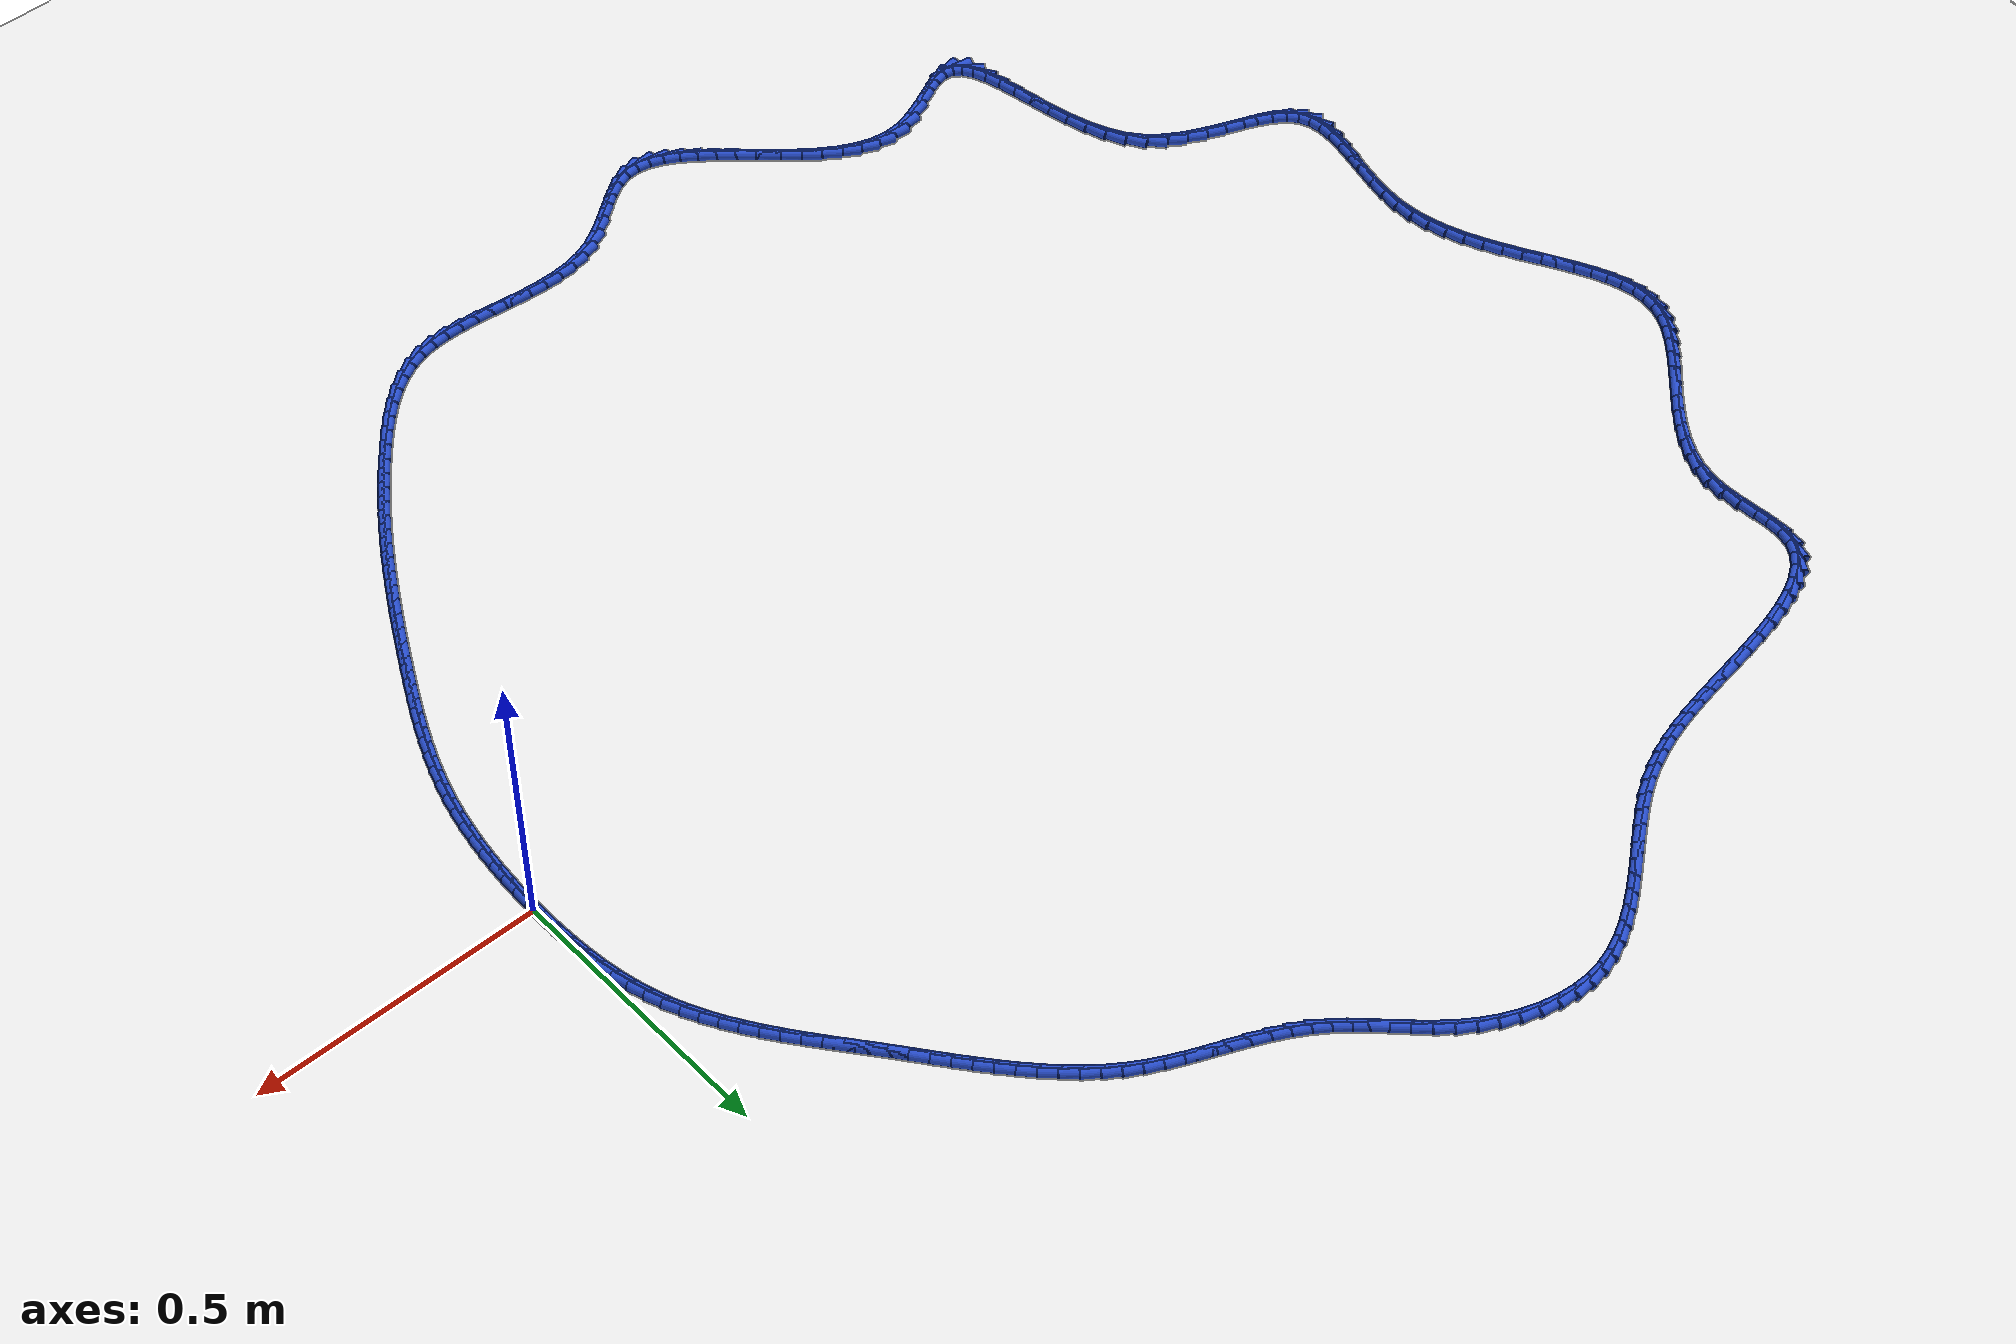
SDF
<sdf version="1.6">
 <world name="default">
  <light name="sun" type="directional">
   <pose>0 0 10 0 -0 0</pose>
   <diffuse>0.8 0.8 0.8 1</diffuse>
   <specular>0.2 0.2 0.2 1</specular>
   <attenuation>
    <range>1000</range>
    <constant>0.9</constant>
    <linear>0.01</linear>
    <quadratic>0.001</quadratic>
   </attenuation>
   <direction>-0.5 0.1 -0.9</direction>
  </light>
  <model name="ground_plane">
   <static>1</static>
   <link name="link">
    <collision name="collision">
     <geometry><plane><normal>0 0 1</normal><size>100 100</size></plane></geometry>
     <surface><friction><ode><mu>100</mu><mu2>50</mu2></ode></friction></surface>
    </collision>
    <visual name="visual">
     <cast_shadows>0</cast_shadows>
     <geometry><plane><normal>0 0 1</normal><size>100 100</size></plane></geometry>
     <material>
      <script><uri>file://media/materials/scripts/gazebo.material</uri><name>Gazebo/WhiteGlow</name></script>
     </material>
    </visual>
   </link>
  </model>
  <gravity>0 0 -9.8</gravity>
  <magnetic_field>6e-06 2.3e-05 -4.2e-05</magnetic_field>
  <atmosphere type="adiabatic"/>
  <physics name="default_physics" default="0" type="ode">
   <max_step_size>0.001</max_step_size>
   <real_time_factor>1</real_time_factor>
   <real_time_update_rate>1000</real_time_update_rate>
  </physics>
  <scene><ambient>0.4 0.4 0.4 1</ambient><background>0.7 0.7 0.7 1</background><shadows>1</shadows></scene>
  <spherical_coordinates>
   <surface_model>EARTH_WGS84</surface_model>
   <latitude_deg>0</latitude_deg>
   <longitude_deg>0</longitude_deg>
   <elevation>0</elevation>
   <heading_deg>0</heading_deg>
  </spherical_coordinates>
  <model name="line">
   <link name="link_0">
    <pose>1.6479873021779667e-17 0.0 0.01 0 1.57 1.5675752540527133</pose>
    <collision name="collision">
     <geometry><cylinder><radius>0.01</radius><length>0.08</length></cylinder></geometry>
    </collision>
    <visual name="visual">
     <material>
      <script><name>Gazebo/Blue</name><uri>file://media/materials/scripts/gazebo.material</uri></script>
     </material>
     <geometry><cylinder><radius>0.01</radius><length>0.08</length></cylinder></geometry>
    </visual>
   </link>
   <link name="link_1">
    <pose>0.0001011087600426013 0.0313896699816783 0.01 0 1.57 -1.5484223017014453</pose>
    <collision name="collision">
     <geometry><cylinder><radius>0.01</radius><length>0.08</length></cylinder></geometry>
    </collision>
    <visual name="visual">
     <material>
      <script><name>Gazebo/Blue</name><uri>file://media/materials/scripts/gazebo.material</uri></script>
     </material>
     <geometry><cylinder><radius>0.01</radius><length>0.08</length></cylinder></geometry>
    </visual>
   </link>
   <link name="link_2">
    <pose>-0.0006017148387606974 0.06279690738424935 0.01 0 1.57 -1.5186276149639046</pose>
    <collision name="collision">
     <geometry><cylinder><radius>0.01</radius><length>0.08</length></cylinder></geometry>
    </collision>
    <visual name="visual">
     <material>
      <script><name>Gazebo/Blue</name><uri>file://media/materials/scripts/gazebo.material</uri></script>
     </material>
     <geometry><cylinder><radius>0.01</radius><length>0.08</length></cylinder></geometry>
    </visual>
   </link>
   <link name="link_3">
    <pose>-0.0022372068500118043 0.09411851721863422 0.01 0 1.57 -1.484386432581348</pose>
    <collision name="collision">
     <geometry><cylinder><radius>0.01</radius><length>0.08</length></cylinder></geometry>
    </collision>
    <visual name="visual">
     <material>
      <script><name>Gazebo/Blue</name><uri>file://media/materials/scripts/gazebo.material</uri></script>
     </material>
     <geometry><cylinder><radius>0.01</radius><length>0.08</length></cylinder></geometry>
    </visual>
   </link>
   <link name="link_4">
    <pose>-0.004934103327312637 0.12525130449575378 0.01 0 1.57 -1.4454217284860233</pose>
    <collision name="collision">
     <geometry><cylinder><radius>0.01</radius><length>0.08</length></cylinder></geometry>
    </collision>
    <visual name="visual">
     <material>
      <script><name>Gazebo/Blue</name><uri>file://media/materials/scripts/gazebo.material</uri></script>
     </material>
     <geometry><cylinder><radius>0.01</radius><length>0.08</length></cylinder></geometry>
    </visual>
   </link>
   <link name="link_5">
    <pose>-0.008821140324265125 0.15609207422652904 0.01 0 1.57 -1.4014432492507192</pose>
    <collision name="collision">
     <geometry><cylinder><radius>0.01</radius><length>0.08</length></cylinder></geometry>
    </collision>
    <visual name="visual">
     <material>
      <script><name>Gazebo/Blue</name><uri>file://media/materials/scripts/gazebo.material</uri></script>
     </material>
     <geometry><cylinder><radius>0.01</radius><length>0.08</length></cylinder></geometry>
    </visual>
   </link>
   <link name="link_6">
    <pose>-0.01402705389447119 0.18653763142188096 0.01 0 1.57 -1.3521718016188053</pose>
    <collision name="collision">
     <geometry><cylinder><radius>0.01</radius><length>0.08</length></cylinder></geometry>
    </collision>
    <visual name="visual">
     <material>
      <script><name>Gazebo/Blue</name><uri>file://media/materials/scripts/gazebo.material</uri></script>
     </material>
     <geometry><cylinder><radius>0.01</radius><length>0.08</length></cylinder></geometry>
    </visual>
   </link>
   <link name="link_7">
    <pose>-0.020680580091532754 0.21648478109273056 0.01 0 1.57 -1.2973730357408915</pose>
    <collision name="collision">
     <geometry><cylinder><radius>0.01</radius><length>0.08</length></cylinder></geometry>
    </collision>
    <visual name="visual">
     <material>
      <script><name>Gazebo/Blue</name><uri>file://media/materials/scripts/gazebo.material</uri></script>
     </material>
     <geometry><cylinder><radius>0.01</radius><length>0.08</length></cylinder></geometry>
    </visual>
   </link>
   <link name="link_8">
    <pose>-0.028910454969051737 0.24583032824999868 0.01 0 1.57 -1.2369107856390804</pose>
    <collision name="collision">
     <geometry><cylinder><radius>0.01</radius><length>0.08</length></cylinder></geometry>
    </collision>
    <visual name="visual">
     <material>
      <script><name>Gazebo/Blue</name><uri>file://media/materials/scripts/gazebo.material</uri></script>
     </material>
     <geometry><cylinder><radius>0.01</radius><length>0.08</length></cylinder></geometry>
    </visual>
   </link>
   <link name="link_9">
    <pose>-0.038845181325287824 0.2744712218505244 0.01 0 1.57 -1.1738996928790446</pose>
    <collision name="collision">
     <geometry><cylinder><radius>0.01</radius><length>0.08</length></cylinder></geometry>
    </collision>
    <visual name="visual">
     <material>
      <script><name>Gazebo/Blue</name><uri>file://media/materials/scripts/gazebo.material</uri></script>
     </material>
     <geometry><cylinder><radius>0.01</radius><length>0.08</length></cylinder></geometry>
    </visual>
   </link>
   <link name="link_10">
    <pose>-0.05053215916598173 0.3023544607912741 0.01 0 1.57 -1.1163393704208906</pose>
    <collision name="collision">
     <geometry><cylinder><radius>0.01</radius><length>0.08</length></cylinder></geometry>
    </collision>
    <visual name="visual">
     <material>
      <script><name>Gazebo/Blue</name><uri>file://media/materials/scripts/gazebo.material</uri></script>
     </material>
     <geometry><cylinder><radius>0.01</radius><length>0.08</length></cylinder></geometry>
    </visual>
   </link>
   <link name="link_11">
    <pose>-0.06381906367342541 0.3295502976223272 0.01 0 1.57 -1.0657681846072646</pose>
    <collision name="collision">
     <geometry><cylinder><radius>0.01</radius><length>0.08</length></cylinder></geometry>
    </collision>
    <visual name="visual">
     <material>
      <script><name>Gazebo/Blue</name><uri>file://media/materials/scripts/gazebo.material</uri></script>
     </material>
     <geometry><cylinder><radius>0.01</radius><length>0.08</length></cylinder></geometry>
    </visual>
   </link>
   <link name="link_12">
    <pose>-0.07852337432375618 0.3561476191878261 0.01 0 1.57 -1.0223385522766313</pose>
    <collision name="collision">
     <geometry><cylinder><radius>0.01</radius><length>0.08</length></cylinder></geometry>
    </collision>
    <visual name="visual">
     <material>
      <script><name>Gazebo/Blue</name><uri>file://media/materials/scripts/gazebo.material</uri></script>
     </material>
     <geometry><cylinder><radius>0.01</radius><length>0.08</length></cylinder></geometry>
    </visual>
   </link>
   <link name="link_13">
    <pose>-0.09446257059311147 0.38223531233191366 0.01 0 1.57 -0.9860303867190535</pose>
    <collision name="collision">
     <geometry><cylinder><radius>0.01</radius><length>0.08</length></cylinder></geometry>
    </collision>
    <visual name="visual">
     <material>
      <script><name>Gazebo/Blue</name><uri>file://media/materials/scripts/gazebo.material</uri></script>
     </material>
     <geometry><cylinder><radius>0.01</radius><length>0.08</length></cylinder></geometry>
    </visual>
   </link>
   <link name="link_14">
    <pose>-0.11145413195762871 0.4079022638987322 0.01 0 1.57 -0.9567182453364077</pose>
    <collision name="collision">
     <geometry><cylinder><radius>0.01</radius><length>0.08</length></cylinder></geometry>
    </collision>
    <visual name="visual">
     <material>
      <script><name>Gazebo/Blue</name><uri>file://media/materials/scripts/gazebo.material</uri></script>
     </material>
     <geometry><cylinder><radius>0.01</radius><length>0.08</length></cylinder></geometry>
    </visual>
   </link>
   <link name="link_15">
    <pose>-0.12931553789344527 0.4332373607324246 0.01 0 1.57 -0.9342269336689711</pose>
    <collision name="collision">
     <geometry><cylinder><radius>0.01</radius><length>0.08</length></cylinder></geometry>
    </collision>
    <visual name="visual">
     <material>
      <script><name>Gazebo/Blue</name><uri>file://media/materials/scripts/gazebo.material</uri></script>
     </material>
     <geometry><cylinder><radius>0.01</radius><length>0.08</length></cylinder></geometry>
    </visual>
   </link>
   <link name="link_16">
    <pose>-0.14786426787669857 0.45832948967713316 0.01 0 1.57 -0.9183733629863463</pose>
    <collision name="collision">
     <geometry><cylinder><radius>0.01</radius><length>0.08</length></cylinder></geometry>
    </collision>
    <visual name="visual">
     <material>
      <script><name>Gazebo/Blue</name><uri>file://media/materials/scripts/gazebo.material</uri></script>
     </material>
     <geometry><cylinder><radius>0.01</radius><length>0.08</length></cylinder></geometry>
    </visual>
   </link>
   <link name="link_17">
    <pose>-0.16691780138352597 0.48326753757700064 0.01 0 1.57 -0.9089954864066254</pose>
    <collision name="collision">
     <geometry><cylinder><radius>0.01</radius><length>0.08</length></cylinder></geometry>
    </collision>
    <visual name="visual">
     <material>
      <script><name>Gazebo/Blue</name><uri>file://media/materials/scripts/gazebo.material</uri></script>
     </material>
     <geometry><cylinder><radius>0.01</radius><length>0.08</length></cylinder></geometry>
    </visual>
   </link>
   <link name="link_18">
    <pose>-0.1862936178900649 0.5081403912761695 0.01 0 1.57 -0.9059703376756326</pose>
    <collision name="collision">
     <geometry><cylinder><radius>0.01</radius><length>0.08</length></cylinder></geometry>
    </collision>
    <visual name="visual">
     <material>
      <script><name>Gazebo/Blue</name><uri>file://media/materials/scripts/gazebo.material</uri></script>
     </material>
     <geometry><cylinder><radius>0.01</radius><length>0.08</length></cylinder></geometry>
    </visual>
   </link>
   <link name="link_19">
    <pose>-0.20580919687245272 0.5330369376187822 0.01 0 1.57 -0.9092200186956592</pose>
    <collision name="collision">
     <geometry><cylinder><radius>0.01</radius><length>0.08</length></cylinder></geometry>
    </collision>
    <visual name="visual">
     <material>
      <script><name>Gazebo/Blue</name><uri>file://media/materials/scripts/gazebo.material</uri></script>
     </material>
     <geometry><cylinder><radius>0.01</radius><length>0.08</length></cylinder></geometry>
    </visual>
   </link>
   <link name="link_20">
    <pose>-0.22528209696572 0.5580459988531922 0.01 0 1.57 -0.9157884607096277</pose>
    <collision name="collision">
     <geometry><cylinder><radius>0.01</radius><length>0.08</length></cylinder></geometry>
    </collision>
    <visual name="visual">
     <material>
      <script><name>Gazebo/Blue</name><uri>file://media/materials/scripts/gazebo.material</uri></script>
     </material>
     <geometry><cylinder><radius>0.01</radius><length>0.08</length></cylinder></geometry>
    </visual>
   </link>
   <link name="link_21">
    <pose>-0.2446019502811583 0.5831975833292085 0.01 0 1.57 -0.9173485451495197</pose>
    <collision name="collision">
     <geometry><cylinder><radius>0.01</radius><length>0.08</length></cylinder></geometry>
    </collision>
    <visual name="visual">
     <material>
      <script><name>Gazebo/Blue</name><uri>file://media/materials/scripts/gazebo.material</uri></script>
     </material>
     <geometry><cylinder><radius>0.01</radius><length>0.08</length></cylinder></geometry>
    </visual>
   </link>
   <link name="link_22">
    <pose>-0.2638634598900939 0.6083543559679153 0.01 0 1.57 -0.912413605386662</pose>
    <collision name="collision">
     <geometry><cylinder><radius>0.01</radius><length>0.08</length></cylinder></geometry>
    </collision>
    <visual name="visual">
     <material>
      <script><name>Gazebo/Blue</name><uri>file://media/materials/scripts/gazebo.material</uri></script>
     </material>
     <geometry><cylinder><radius>0.01</radius><length>0.08</length></cylinder></geometry>
    </visual>
   </link>
   <link name="link_23">
    <pose>-0.2831975582210198 0.6333494175588017 0.01 0 1.57 -0.9009079107747728</pose>
    <collision name="collision">
     <geometry><cylinder><radius>0.01</radius><length>0.08</length></cylinder></geometry>
    </collision>
    <visual name="visual">
     <material>
      <script><name>Gazebo/Blue</name><uri>file://media/materials/scripts/gazebo.material</uri></script>
     </material>
     <geometry><cylinder><radius>0.01</radius><length>0.08</length></cylinder></geometry>
    </visual>
   </link>
   <link name="link_24">
    <pose>-0.3027351777024291 0.6580158688913568 0.01 0 1.57 -0.8826961027737683</pose>
    <collision name="collision">
     <geometry><cylinder><radius>0.01</radius><length>0.08</length></cylinder></geometry>
    </collision>
    <visual name="visual">
     <material>
      <script><name>Gazebo/Blue</name><uri>file://media/materials/scripts/gazebo.material</uri></script>
     </material>
     <geometry><cylinder><radius>0.01</radius><length>0.08</length></cylinder></geometry>
    </visual>
   </link>
   <link name="link_25">
    <pose>-0.3226072507628147 0.6821868107550688 0.01 0 1.57 -0.8575954692149445</pose>
    <collision name="collision">
     <geometry><cylinder><radius>0.01</radius><length>0.08</length></cylinder></geometry>
    </collision>
    <visual name="visual">
     <material>
      <script><name>Gazebo/Blue</name><uri>file://media/materials/scripts/gazebo.material</uri></script>
     </material>
     <geometry><cylinder><radius>0.01</radius><length>0.08</length></cylinder></geometry>
    </visual>
   </link>
   <link name="link_26">
    <pose>-0.3429447098306698 0.7056953439394272 0.01 0 1.57 -0.8253980872158135</pose>
    <collision name="collision">
     <geometry><cylinder><radius>0.01</radius><length>0.08</length></cylinder></geometry>
    </collision>
    <visual name="visual">
     <material>
      <script><name>Gazebo/Blue</name><uri>file://media/materials/scripts/gazebo.material</uri></script>
     </material>
     <geometry><cylinder><radius>0.01</radius><length>0.08</length></cylinder></geometry>
    </visual>
   </link>
   <link name="link_27">
    <pose>-0.3638784873344875 0.728374569233921 0.01 0 1.57 -0.7859054954465313</pose>
    <collision name="collision">
     <geometry><cylinder><radius>0.01</radius><length>0.08</length></cylinder></geometry>
    </collision>
    <visual name="visual">
     <material>
      <script><name>Gazebo/Blue</name><uri>file://media/materials/scripts/gazebo.material</uri></script>
     </material>
     <geometry><cylinder><radius>0.01</radius><length>0.08</length></cylinder></geometry>
    </visual>
   </link>
   <link name="link_28">
    <pose>-0.38553951570276085 0.750057587428039 0.01 0 1.57 -0.7389784553765539</pose>
    <collision name="collision">
     <geometry><cylinder><radius>0.01</radius><length>0.08</length></cylinder></geometry>
    </collision>
    <visual name="visual">
     <material>
      <script><name>Gazebo/Blue</name><uri>file://media/materials/scripts/gazebo.material</uri></script>
     </material>
     <geometry><cylinder><radius>0.01</radius><length>0.08</length></cylinder></geometry>
    </visual>
   </link>
   <link name="link_29">
    <pose>-0.4080587273639827 0.7705774993112697 0.01 0 1.57 -0.6846027420597098</pose>
    <collision name="collision">
     <geometry><cylinder><radius>0.01</radius><length>0.08</length></cylinder></geometry>
    </collision>
    <visual name="visual">
     <material>
      <script><name>Gazebo/Blue</name><uri>file://media/materials/scripts/gazebo.material</uri></script>
     </material>
     <geometry><cylinder><radius>0.01</radius><length>0.08</length></cylinder></geometry>
    </visual>
   </link>
   <link name="link_30">
    <pose>-0.4315670547466465 0.7897674056731028 0.01 0 1.57 -0.6229678870915362</pose>
    <collision name="collision">
     <geometry><cylinder><radius>0.01</radius><length>0.08</length></cylinder></geometry>
    </collision>
    <visual name="visual">
     <material>
      <script><name>Gazebo/Blue</name><uri>file://media/materials/scripts/gazebo.material</uri></script>
     </material>
     <geometry><cylinder><radius>0.01</radius><length>0.08</length></cylinder></geometry>
    </visual>
   </link>
   <link name="link_31">
    <pose>-0.456195430279245 0.8074604073030268 0.01 0 1.57 -0.5547058360312105</pose>
    <collision name="collision">
     <geometry><cylinder><radius>0.01</radius><length>0.08</length></cylinder></geometry>
    </collision>
    <visual name="visual">
     <material>
      <script><name>Gazebo/Blue</name><uri>file://media/materials/scripts/gazebo.material</uri></script>
     </material>
     <geometry><cylinder><radius>0.01</radius><length>0.08</length></cylinder></geometry>
    </visual>
   </link>
   <link name="link_32">
    <pose>-0.4820718744353938 0.8234934196681538 0.01 0 1.57 -0.48992020300903294</pose>
    <collision name="collision">
     <geometry><cylinder><radius>0.01</radius><length>0.08</length></cylinder></geometry>
    </collision>
    <visual name="visual">
     <material>
      <script><name>Gazebo/Blue</name><uri>file://media/materials/scripts/gazebo.material</uri></script>
     </material>
     <geometry><cylinder><radius>0.01</radius><length>0.08</length></cylinder></geometry>
    </visual>
   </link>
   <link name="link_33">
    <pose>-0.5091489354954488 0.8379332278171359 0.01 0 1.57 -0.4431651346322764</pose>
    <collision name="collision">
     <geometry><cylinder><radius>0.01</radius><length>0.08</length></cylinder></geometry>
    </collision>
    <visual name="visual">
     <material>
      <script><name>Gazebo/Blue</name><uri>file://media/materials/scripts/gazebo.material</uri></script>
     </material>
     <geometry><cylinder><radius>0.01</radius><length>0.08</length></cylinder></geometry>
    </visual>
   </link>
   <link name="link_34">
    <pose>-0.5371067448820345 0.8512034844477239 0.01 0 1.57 -0.4150134319221276</pose>
    <collision name="collision">
     <geometry><cylinder><radius>0.01</radius><length>0.08</length></cylinder></geometry>
    </collision>
    <visual name="visual">
     <material>
      <script><name>Gazebo/Blue</name><uri>file://media/materials/scripts/gazebo.material</uri></script>
     </material>
     <geometry><cylinder><radius>0.01</radius><length>0.08</length></cylinder></geometry>
    </visual>
   </link>
   <link name="link_35">
    <pose>-0.5656019493991258 0.8637586072430574 0.01 0 1.57 -0.40486278913823814</pose>
    <collision name="collision">
     <geometry><cylinder><radius>0.01</radius><length>0.08</length></cylinder></geometry>
    </collision>
    <visual name="visual">
     <material>
      <script><name>Gazebo/Blue</name><uri>file://media/materials/scripts/gazebo.material</uri></script>
     </material>
     <geometry><cylinder><radius>0.01</radius><length>0.08</length></cylinder></geometry>
    </visual>
   </link>
   <link name="link_36">
    <pose>-0.5942911958506975 0.876053013886275 0.01 0 1.57 -0.41246592205005195</pose>
    <collision name="collision">
     <geometry><cylinder><radius>0.01</radius><length>0.08</length></cylinder></geometry>
    </collision>
    <visual name="visual">
     <material>
      <script><name>Gazebo/Blue</name><uri>file://media/materials/scripts/gazebo.material</uri></script>
     </material>
     <geometry><cylinder><radius>0.01</radius><length>0.08</length></cylinder></geometry>
    </visual>
   </link>
   <link name="link_37">
    <pose>-0.6228311310407245 0.8885411220605159 0.01 0 1.57 -0.4380169923599859</pose>
    <collision name="collision">
     <geometry><cylinder><radius>0.01</radius><length>0.08</length></cylinder></geometry>
    </collision>
    <visual name="visual">
     <material>
      <script><name>Gazebo/Blue</name><uri>file://media/materials/scripts/gazebo.material</uri></script>
     </material>
     <geometry><cylinder><radius>0.01</radius><length>0.08</length></cylinder></geometry>
    </visual>
   </link>
   <link name="link_38">
    <pose>-0.6508784017731817 0.9016773494489193 0.01 0 1.57 -0.48208787309147416</pose>
    <collision name="collision">
     <geometry><cylinder><radius>0.01</radius><length>0.08</length></cylinder></geometry>
    </collision>
    <visual name="visual">
     <material>
      <script><name>Gazebo/Blue</name><uri>file://media/materials/scripts/gazebo.material</uri></script>
     </material>
     <geometry><cylinder><radius>0.01</radius><length>0.08</length></cylinder></geometry>
    </visual>
   </link>
   <link name="link_39">
    <pose>-0.6780896548520442 0.9159161137346242 0.01 0 1.57 -0.5453925074964361</pose>
    <collision name="collision">
     <geometry><cylinder><radius>0.01</radius><length>0.08</length></cylinder></geometry>
    </collision>
    <visual name="visual">
     <material>
      <script><name>Gazebo/Blue</name><uri>file://media/materials/scripts/gazebo.material</uri></script>
     </material>
     <geometry><cylinder><radius>0.01</radius><length>0.08</length></cylinder></geometry>
    </visual>
   </link>
   <link name="link_40">
    <pose>-0.7041215370812866 0.9317118326007694 0.01 0 1.57 -0.6264170707911787</pose>
    <collision name="collision">
     <geometry><cylinder><radius>0.01</radius><length>0.08</length></cylinder></geometry>
    </collision>
    <visual name="visual">
     <material>
      <script><name>Gazebo/Blue</name><uri>file://media/materials/scripts/gazebo.material</uri></script>
     </material>
     <geometry><cylinder><radius>0.01</radius><length>0.08</length></cylinder></geometry>
    </visual>
   </link>
   <link name="link_41">
    <pose>-0.7286673550544754 0.9494742017059244 0.01 0 1.57 -0.6998584969151953</pose>
    <collision name="collision">
     <geometry><cylinder><radius>0.01</radius><length>0.08</length></cylinder></geometry>
    </collision>
    <visual name="visual">
     <material>
      <script><name>Gazebo/Blue</name><uri>file://media/materials/scripts/gazebo.material</uri></script>
     </material>
     <geometry><cylinder><radius>0.01</radius><length>0.08</length></cylinder></geometry>
    </visual>
   </link>
   <link name="link_42">
    <pose>-0.7518954859493154 0.9690333684195619 0.01 0 1.57 -0.7477128982914095</pose>
    <collision name="collision">
     <geometry><cylinder><radius>0.01</radius><length>0.08</length></cylinder></geometry>
    </collision>
    <visual name="visual">
     <material>
      <script><name>Gazebo/Blue</name><uri>file://media/materials/scripts/gazebo.material</uri></script>
     </material>
     <geometry><cylinder><radius>0.01</radius><length>0.08</length></cylinder></geometry>
    </visual>
   </link>
   <link name="link_43">
    <pose>-0.7743057446235722 0.9898151525294567 0.01 0 1.57 -0.7698439479143578</pose>
    <collision name="collision">
     <geometry><cylinder><radius>0.01</radius><length>0.08</length></cylinder></geometry>
    </collision>
    <visual name="visual">
     <material>
      <script><name>Gazebo/Blue</name><uri>file://media/materials/scripts/gazebo.material</uri></script>
     </material>
     <geometry><cylinder><radius>0.01</radius><length>0.08</length></cylinder></geometry>
    </visual>
   </link>
   <link name="link_44">
    <pose>-0.79640470680429 1.0112371261011406 0.01 0 1.57 -0.7667932204810358</pose>
    <collision name="collision">
     <geometry><cylinder><radius>0.01</radius><length>0.08</length></cylinder></geometry>
    </collision>
    <visual name="visual">
     <material>
      <script><name>Gazebo/Blue</name><uri>file://media/materials/scripts/gazebo.material</uri></script>
     </material>
     <geometry><cylinder><radius>0.01</radius><length>0.08</length></cylinder></geometry>
    </visual>
   </link>
   <link name="link_45">
    <pose>-0.8186989482185141 1.0327168612001452 0.01 0 1.57 -0.7389929681970252</pose>
    <collision name="collision">
     <geometry><cylinder><radius>0.01</radius><length>0.08</length></cylinder></geometry>
    </collision>
    <visual name="visual">
     <material>
      <script><name>Gazebo/Blue</name><uri>file://media/materials/scripts/gazebo.material</uri></script>
     </material>
     <geometry><cylinder><radius>0.01</radius><length>0.08</length></cylinder></geometry>
    </visual>
   </link>
   <link name="link_46">
    <pose>-0.841695044593289 1.0536719298920016 0.01 0 1.57 -0.6868241260423399</pose>
    <collision name="collision">
     <geometry><cylinder><radius>0.01</radius><length>0.08</length></cylinder></geometry>
    </collision>
    <visual name="visual">
     <material>
      <script><name>Gazebo/Blue</name><uri>file://media/materials/scripts/gazebo.material</uri></script>
     </material>
     <geometry><cylinder><radius>0.01</radius><length>0.08</length></cylinder></geometry>
    </visual>
   </link>
   <link name="link_47">
    <pose>-0.8658995716556599 1.073519904242242 0.01 0 1.57 -0.6113152807213914</pose>
    <collision name="collision">
     <geometry><cylinder><radius>0.01</radius><length>0.08</length></cylinder></geometry>
    </collision>
    <visual name="visual">
     <material>
      <script><name>Gazebo/Blue</name><uri>file://media/materials/scripts/gazebo.material</uri></script>
     </material>
     <geometry><cylinder><radius>0.01</radius><length>0.08</length></cylinder></geometry>
    </visual>
   </link>
   <link name="link_48">
    <pose>-0.891810783431696 1.0916805140291534 0.01 0 1.57 -0.5230464651785506</pose>
    <collision name="collision">
     <geometry><cylinder><radius>0.01</radius><length>0.08</length></cylinder></geometry>
    </collision>
    <visual name="visual">
     <material>
      <script><name>Gazebo/Blue</name><uri>file://media/materials/scripts/gazebo.material</uri></script>
     </material>
     <geometry><cylinder><radius>0.01</radius><length>0.08</length></cylinder></geometry>
    </visual>
   </link>
   <link name="link_49">
    <pose>-0.9195450785254147 1.107672499355635 0.01 0 1.57 -0.4332704797082813</pose>
    <collision name="collision">
     <geometry><cylinder><radius>0.01</radius><length>0.08</length></cylinder></geometry>
    </collision>
    <visual name="visual">
     <material>
      <script><name>Gazebo/Blue</name><uri>file://media/materials/scripts/gazebo.material</uri></script>
     </material>
     <geometry><cylinder><radius>0.01</radius><length>0.08</length></cylinder></geometry>
    </visual>
   </link>
   <link name="link_50">
    <pose>-0.9486861388794618 1.1211527270776018 0.01 0 1.57 -0.3397328080729792</pose>
    <collision name="collision">
     <geometry><cylinder><radius>0.01</radius><length>0.08</length></cylinder></geometry>
    </collision>
    <visual name="visual">
     <material>
      <script><name>Gazebo/Blue</name><uri>file://media/materials/scripts/gazebo.material</uri></script>
     </material>
     <geometry><cylinder><radius>0.01</radius><length>0.08</length></cylinder></geometry>
    </visual>
   </link>
   <link name="link_51">
    <pose>-0.9787781000762972 1.1317883179264738 0.01 0 1.57 -0.2391646798696684</pose>
    <collision name="collision">
     <geometry><cylinder><radius>0.01</radius><length>0.08</length></cylinder></geometry>
    </collision>
    <visual name="visual">
     <material>
      <script><name>Gazebo/Blue</name><uri>file://media/materials/scripts/gazebo.material</uri></script>
     </material>
     <geometry><cylinder><radius>0.01</radius><length>0.08</length></cylinder></geometry>
    </visual>
   </link>
   <link name="link_52">
    <pose>-1.0093650976983803 1.1392463926336716 0.01 0 1.57 -0.12819204238329432</pose>
    <collision name="collision">
     <geometry><cylinder><radius>0.01</radius><length>0.08</length></cylinder></geometry>
    </collision>
    <visual name="visual">
     <material>
      <script><name>Gazebo/Blue</name><uri>file://media/materials/scripts/gazebo.material</uri></script>
     </material>
     <geometry><cylinder><radius>0.01</radius><length>0.08</length></cylinder></geometry>
    </visual>
   </link>
   <link name="link_53">
    <pose>-1.0399912673281722 1.1431940719306162 0.01 0 1.57 -0.0034560082480642167</pose>
    <collision name="collision">
     <geometry><cylinder><radius>0.01</radius><length>0.08</length></cylinder></geometry>
    </collision>
    <visual name="visual">
     <material>
      <script><name>Gazebo/Blue</name><uri>file://media/materials/scripts/gazebo.material</uri></script>
     </material>
     <geometry><cylinder><radius>0.01</radius><length>0.08</length></cylinder></geometry>
    </visual>
   </link>
   <link name="link_54">
    <pose>-1.0702007445481323 1.1432984765487277 0.01 0 1.57 0.13528638625287295</pose>
    <collision name="collision">
     <geometry><cylinder><radius>0.01</radius><length>0.08</length></cylinder></geometry>
    </collision>
    <visual name="visual">
     <material>
      <script><name>Gazebo/Blue</name><uri>file://media/materials/scripts/gazebo.material</uri></script>
     </material>
     <geometry><cylinder><radius>0.01</radius><length>0.08</length></cylinder></geometry>
    </visual>
   </link>
   <link name="link_55">
    <pose>-1.0995854276476462 1.1392986972730166 0.01 0 1.57 0.267959387349577</pose>
    <collision name="collision">
     <geometry><cylinder><radius>0.01</radius><length>0.08</length></cylinder></geometry>
    </collision>
    <visual name="visual">
     <material>
      <script><name>Gazebo/Blue</name><uri>file://media/materials/scripts/gazebo.material</uri></script>
     </material>
     <geometry><cylinder><radius>0.01</radius><length>0.08</length></cylinder></geometry>
    </visual>
   </link>
   <link name="link_56">
    <pose>-1.12809393031731 1.1314713326679728 0.01 0 1.57 0.3816964095908053</pose>
    <collision name="collision">
     <geometry><cylinder><radius>0.01</radius><length>0.08</length></cylinder></geometry>
    </collision>
    <visual name="visual">
     <material>
      <script><name>Gazebo/Blue</name><uri>file://media/materials/scripts/gazebo.material</uri></script>
     </material>
     <geometry><cylinder><radius>0.01</radius><length>0.08</length></cylinder></geometry>
    </visual>
   </link>
   <link name="link_57">
    <pose>-1.1558362141451612 1.1203361043866404 0.01 0 1.57 0.47477163738193723</pose>
    <collision name="collision">
     <geometry><cylinder><radius>0.01</radius><length>0.08</length></cylinder></geometry>
    </collision>
    <visual name="visual">
     <material>
      <script><name>Gazebo/Blue</name><uri>file://media/materials/scripts/gazebo.material</uri></script>
     </material>
     <geometry><cylinder><radius>0.01</radius><length>0.08</length></cylinder></geometry>
    </visual>
   </link>
   <link name="link_58">
    <pose>-1.1829230337664418 1.1064139290656299 0.01 0 1.57 0.5476718748757278</pose>
    <collision name="collision">
     <geometry><cylinder><radius>0.01</radius><length>0.08</length></cylinder></geometry>
    </collision>
    <visual name="visual">
     <material>
      <script><name>Gazebo/Blue</name><uri>file://media/materials/scripts/gazebo.material</uri></script>
     </material>
     <geometry><cylinder><radius>0.01</radius><length>0.08</length></cylinder></geometry>
    </visual>
   </link>
   <link name="link_59">
    <pose>-1.209465143816394 1.0902257233415507 0.01 0 1.57 0.6018701174483252</pose>
    <collision name="collision">
     <geometry><cylinder><radius>0.01</radius><length>0.08</length></cylinder></geometry>
    </collision>
    <visual name="visual">
     <material>
      <script><name>Gazebo/Blue</name><uri>file://media/materials/scripts/gazebo.material</uri></script>
     </material>
     <geometry><cylinder><radius>0.01</radius><length>0.08</length></cylinder></geometry>
    </visual>
   </link>
   <link name="link_60">
    <pose>-1.235573298930259 1.0722924038510127 0.01 0 1.57 0.6389884237398049</pose>
    <collision name="collision">
     <geometry><cylinder><radius>0.01</radius><length>0.08</length></cylinder></geometry>
    </collision>
    <visual name="visual">
     <material>
      <script><name>Gazebo/Blue</name><uri>file://media/materials/scripts/gazebo.material</uri></script>
     </material>
     <geometry><cylinder><radius>0.01</radius><length>0.08</length></cylinder></geometry>
    </visual>
   </link>
   <link name="link_61">
    <pose>-1.2613582537432801 1.0531348872306256 0.01 0 1.57 0.6603378455330079</pose>
    <collision name="collision">
     <geometry><cylinder><radius>0.01</radius><length>0.08</length></cylinder></geometry>
    </collision>
    <visual name="visual">
     <material>
      <script><name>Gazebo/Blue</name><uri>file://media/materials/scripts/gazebo.material</uri></script>
     </material>
     <geometry><cylinder><radius>0.01</radius><length>0.08</length></cylinder></geometry>
    </visual>
   </link>
   <link name="link_62">
    <pose>-1.2869307628906987 1.0332740901170003 0.01 0 1.57 0.6667061618446942</pose>
    <collision name="collision">
     <geometry><cylinder><radius>0.01</radius><length>0.08</length></cylinder></geometry>
    </collision>
    <visual name="visual">
     <material>
      <script><name>Gazebo/Blue</name><uri>file://media/materials/scripts/gazebo.material</uri></script>
     </material>
     <geometry><cylinder><radius>0.01</radius><length>0.08</length></cylinder></geometry>
    </visual>
   </link>
   <link name="link_63">
    <pose>-1.3124015810077565 1.0132309291467452 0.01 0 1.57 0.6582720526338149</pose>
    <collision name="collision">
     <geometry><cylinder><radius>0.01</radius><length>0.08</length></cylinder></geometry>
    </collision>
    <visual name="visual">
     <material>
      <script><name>Gazebo/Blue</name><uri>file://media/materials/scripts/gazebo.material</uri></script>
     </material>
     <geometry><cylinder><radius>0.01</radius><length>0.08</length></cylinder></geometry>
    </visual>
   </link>
   <link name="link_64">
    <pose>-1.3378814627296964 0.9935263209564712 0.01 0 1.57 0.6345759876998177</pose>
    <collision name="collision">
     <geometry><cylinder><radius>0.01</radius><length>0.08</length></cylinder></geometry>
    </collision>
    <visual name="visual">
     <material>
      <script><name>Gazebo/Blue</name><uri>file://media/materials/scripts/gazebo.material</uri></script>
     </material>
     <geometry><cylinder><radius>0.01</radius><length>0.08</length></cylinder></geometry>
    </visual>
   </link>
   <link name="link_65">
    <pose>-1.363481162691759 0.9746811821827874 0.01 0 1.57 0.5945290219341868</pose>
    <collision name="collision">
     <geometry><cylinder><radius>0.01</radius><length>0.08</length></cylinder></geometry>
    </collision>
    <visual name="visual">
     <material>
      <script><name>Gazebo/Blue</name><uri>file://media/materials/scripts/gazebo.material</uri></script>
     </material>
     <geometry><cylinder><radius>0.01</radius><length>0.08</length></cylinder></geometry>
    </visual>
   </link>
   <link name="link_66">
    <pose>-1.3893114355291878 0.9572164294623045 0.01 0 1.57 0.5364926561047353</pose>
    <collision name="collision">
     <geometry><cylinder><radius>0.01</radius><length>0.08</length></cylinder></geometry>
    </collision>
    <visual name="visual">
     <material>
      <script><name>Gazebo/Blue</name><uri>file://media/materials/scripts/gazebo.material</uri></script>
     </material>
     <geometry><cylinder><radius>0.01</radius><length>0.08</length></cylinder></geometry>
    </visual>
   </link>
   <link name="link_67">
    <pose>-1.4154830363205189 0.9416529108095737 0.01 0 1.57 0.4636962202911939</pose>
    <collision name="collision">
     <geometry><cylinder><radius>0.01</radius><length>0.08</length></cylinder></geometry>
    </collision>
    <visual name="visual">
     <material>
      <script><name>Gazebo/Blue</name><uri>file://media/materials/scripts/gazebo.material</uri></script>
     </material>
     <geometry><cylinder><radius>0.01</radius><length>0.08</length></cylinder></geometry>
    </visual>
   </link>
   <link name="link_68">
    <pose>-1.4421078350065983 0.9283388935949337 0.01 0 1.57 0.39261419955952964</pose>
    <collision name="collision">
     <geometry><cylinder><radius>0.01</radius><length>0.08</length></cylinder></geometry>
    </collision>
    <visual name="visual">
     <material>
      <script><name>Gazebo/Blue</name><uri>file://media/materials/scripts/gazebo.material</uri></script>
     </material>
     <geometry><cylinder><radius>0.01</radius><length>0.08</length></cylinder></geometry>
    </visual>
   </link>
   <link name="link_69">
    <pose>-1.4693012216646817 0.9170777282022049 0.01 0 1.57 0.32882199034700965</pose>
    <collision name="collision">
     <geometry><cylinder><radius>0.01</radius><length>0.08</length></cylinder></geometry>
    </collision>
    <visual name="visual">
     <material>
      <script><name>Gazebo/Blue</name><uri>file://media/materials/scripts/gazebo.material</uri></script>
     </material>
     <geometry><cylinder><radius>0.01</radius><length>0.08</length></cylinder></geometry>
    </visual>
   </link>
   <link name="link_70">
    <pose>-1.497179279434528 0.9075654789654604 0.01 0 1.57 0.274211165654365</pose>
    <collision name="collision">
     <geometry><cylinder><radius>0.01</radius><length>0.08</length></cylinder></geometry>
    </collision>
    <visual name="visual">
     <material>
      <script><name>Gazebo/Blue</name><uri>file://media/materials/scripts/gazebo.material</uri></script>
     </material>
     <geometry><cylinder><radius>0.01</radius><length>0.08</length></cylinder></geometry>
    </visual>
   </link>
   <link name="link_71">
    <pose>-1.5258580914558948 0.8994982102187736 0.01 0 1.57 0.22989105613551558</pose>
    <collision name="collision">
     <geometry><cylinder><radius>0.01</radius><length>0.08</length></cylinder></geometry>
    </collision>
    <visual name="visual">
     <material>
      <script><name>Gazebo/Blue</name><uri>file://media/materials/scripts/gazebo.material</uri></script>
     </material>
     <geometry><cylinder><radius>0.01</radius><length>0.08</length></cylinder></geometry>
    </visual>
   </link>
   <link name="link_72">
    <pose>-1.555453740868541 0.8925719862962173 0.01 0 1.57 0.19624631797527334</pose>
    <collision name="collision">
     <geometry><cylinder><radius>0.01</radius><length>0.08</length></cylinder></geometry>
    </collision>
    <visual name="visual">
     <material>
      <script><name>Gazebo/Blue</name><uri>file://media/materials/scripts/gazebo.material</uri></script>
     </material>
     <geometry><cylinder><radius>0.01</radius><length>0.08</length></cylinder></geometry>
    </visual>
   </link>
   <link name="link_73">
    <pose>-1.5860823108122246 0.8864828715318653 0.01 0 1.57 0.17308889906790426</pose>
    <collision name="collision">
     <geometry><cylinder><radius>0.01</radius><length>0.08</length></cylinder></geometry>
    </collision>
    <visual name="visual">
     <material>
      <script><name>Gazebo/Blue</name><uri>file://media/materials/scripts/gazebo.material</uri></script>
     </material>
     <geometry><cylinder><radius>0.01</radius><length>0.08</length></cylinder></geometry>
    </visual>
   </link>
   <link name="link_74">
    <pose>-1.617859884426704 0.8809269302597903 0.01 0 1.57 0.15983177312235988</pose>
    <collision name="collision">
     <geometry><cylinder><radius>0.01</radius><length>0.08</length></cylinder></geometry>
    </collision>
    <visual name="visual">
     <material>
      <script><name>Gazebo/Blue</name><uri>file://media/materials/scripts/gazebo.material</uri></script>
     </material>
     <geometry><cylinder><radius>0.01</radius><length>0.08</length></cylinder></geometry>
    </visual>
   </link>
   <link name="link_75">
    <pose>-1.650902544851737 0.8756002268140655 0.01 0 1.57 0.1556925260572796</pose>
    <collision name="collision">
     <geometry><cylinder><radius>0.01</radius><length>0.08</length></cylinder></geometry>
    </collision>
    <visual name="visual">
     <material>
      <script><name>Gazebo/Blue</name><uri>file://media/materials/scripts/gazebo.material</uri></script>
     </material>
     <geometry><cylinder><radius>0.01</radius><length>0.08</length></cylinder></geometry>
    </visual>
   </link>
   <link name="link_76">
    <pose>-1.6853179602456794 0.8701982851758795 0.01 0 1.57 0.16208183649633973</pose>
    <collision name="collision">
     <geometry><cylinder><radius>0.01</radius><length>0.08</length></cylinder></geometry>
    </collision>
    <visual name="visual">
     <material>
      <script><name>Gazebo/Blue</name><uri>file://media/materials/scripts/gazebo.material</uri></script>
     </material>
     <geometry><cylinder><radius>0.01</radius><length>0.08</length></cylinder></geometry>
    </visual>
   </link>
   <link name="link_77">
    <pose>-1.7208278295190356 0.864391845005864 0.01 0 1.57 0.18169004166233904</pose>
    <collision name="collision">
     <geometry><cylinder><radius>0.01</radius><length>0.08</length></cylinder></geometry>
    </collision>
    <visual name="visual">
     <material>
      <script><name>Gazebo/Blue</name><uri>file://media/materials/scripts/gazebo.material</uri></script>
     </material>
     <geometry><cylinder><radius>0.01</radius><length>0.08</length></cylinder></geometry>
    </visual>
   </link>
   <link name="link_78">
    <pose>-1.7566154922700523 0.8578170761903919 0.01 0 1.57 0.21556258383382973</pose>
    <collision name="collision">
     <geometry><cylinder><radius>0.01</radius><length>0.08</length></cylinder></geometry>
    </collision>
    <visual name="visual">
     <material>
      <script><name>Gazebo/Blue</name><uri>file://media/materials/scripts/gazebo.material</uri></script>
     </material>
     <geometry><cylinder><radius>0.01</radius><length>0.08</length></cylinder></geometry>
    </visual>
   </link>
   <link name="link_79">
    <pose>-1.7918243331741353 0.8501075829823794 0.01 0 1.57 0.26624336954003286</pose>
    <collision name="collision">
     <geometry><cylinder><radius>0.01</radius><length>0.08</length></cylinder></geometry>
    </collision>
    <visual name="visual">
     <material>
      <script><name>Gazebo/Blue</name><uri>file://media/materials/scripts/gazebo.material</uri></script>
     </material>
     <geometry><cylinder><radius>0.01</radius><length>0.08</length></cylinder></geometry>
    </visual>
   </link>
   <link name="link_80">
    <pose>-1.8255977369066885 0.8408969696347424 0.01 0 1.57 0.3383619925845333</pose>
    <collision name="collision">
     <geometry><cylinder><radius>0.01</radius><length>0.08</length></cylinder></geometry>
    </collision>
    <visual name="visual">
     <material>
      <script><name>Gazebo/Blue</name><uri>file://media/materials/scripts/gazebo.material</uri></script>
     </material>
     <geometry><cylinder><radius>0.01</radius><length>0.08</length></cylinder></geometry>
    </visual>
   </link>
   <link name="link_81">
    <pose>-1.8570790881431165 0.8298188404003967 0.01 0 1.57 0.4392359835745471</pose>
    <collision name="collision">
     <geometry><cylinder><radius>0.01</radius><length>0.08</length></cylinder></geometry>
    </collision>
    <visual name="visual">
     <material>
      <script><name>Gazebo/Blue</name><uri>file://media/materials/scripts/gazebo.material</uri></script>
     </material>
     <geometry><cylinder><radius>0.01</radius><length>0.08</length></cylinder></geometry>
    </visual>
   </link>
   <link name="link_82">
    <pose>-1.8854117715588237 0.8165067995322585 0.01 0 1.57 0.5792461918900362</pose>
    <collision name="collision">
     <geometry><cylinder><radius>0.01</radius><length>0.08</length></cylinder></geometry>
    </collision>
    <visual name="visual">
     <material>
      <script><name>Gazebo/Blue</name><uri>file://media/materials/scripts/gazebo.material</uri></script>
     </material>
     <geometry><cylinder><radius>0.01</radius><length>0.08</length></cylinder></geometry>
    </visual>
   </link>
   <link name="link_83">
    <pose>-1.9097391718292154 0.8005944512832435 0.01 0 1.57 0.770105125531339</pose>
    <collision name="collision">
     <geometry><cylinder><radius>0.01</radius><length>0.08</length></cylinder></geometry>
    </collision>
    <visual name="visual">
     <material>
      <script><name>Gazebo/Blue</name><uri>file://media/materials/scripts/gazebo.material</uri></script>
     </material>
     <geometry><cylinder><radius>0.01</radius><length>0.08</length></cylinder></geometry>
    </visual>
   </link>
   <link name="link_84">
    <pose>-1.9292046736296953 0.7817153999062683 0.01 0 1.57 1.0165991977710864</pose>
    <collision name="collision">
     <geometry><cylinder><radius>0.01</radius><length>0.08</length></cylinder></geometry>
    </collision>
    <visual name="visual">
     <material>
      <script><name>Gazebo/Blue</name><uri>file://media/materials/scripts/gazebo.material</uri></script>
     </material>
     <geometry><cylinder><radius>0.01</radius><length>0.08</length></cylinder></geometry>
    </visual>
   </link>
   <link name="link_85">
    <pose>-1.9429516616356688 0.7595032496542484 0.01 0 1.57 1.2948739624009908</pose>
    <collision name="collision">
     <geometry><cylinder><radius>0.01</radius><length>0.08</length></cylinder></geometry>
    </collision>
    <visual name="visual">
     <material>
      <script><name>Gazebo/Blue</name><uri>file://media/materials/scripts/gazebo.material</uri></script>
     </material>
     <geometry><cylinder><radius>0.01</radius><length>0.08</length></cylinder></geometry>
    </visual>
   </link>
   <link name="link_86">
    <pose>-1.9502702571986594 0.7336557009542304 0.01 0 1.57 1.5037328987565557</pose>
    <collision name="collision">
     <geometry><cylinder><radius>0.01</radius><length>0.08</length></cylinder></geometry>
    </collision>
    <visual name="visual">
     <material>
      <script><name>Gazebo/Blue</name><uri>file://media/materials/scripts/gazebo.material</uri></script>
     </material>
     <geometry><cylinder><radius>0.01</radius><length>0.08</length></cylinder></geometry>
    </visual>
   </link>
   <link name="link_87">
    <pose>-1.9522188795586517 0.7046428659599684 0.01 0 1.57 -1.5326147852702243</pose>
    <collision name="collision">
     <geometry><cylinder><radius>0.01</radius><length>0.08</length></cylinder></geometry>
    </collision>
    <visual name="visual">
     <material>
      <script><name>Gazebo/Blue</name><uri>file://media/materials/scripts/gazebo.material</uri></script>
     </material>
     <geometry><cylinder><radius>0.01</radius><length>0.08</length></cylinder></geometry>
    </visual>
   </link>
   <link name="link_88">
    <pose>-1.9510271735653084 0.6734464608945538 0.01 0 1.57 -1.506620479218856</pose>
    <collision name="collision">
     <geometry><cylinder><radius>0.01</radius><length>0.08</length></cylinder></geometry>
    </collision>
    <visual name="visual">
     <material>
      <script><name>Gazebo/Blue</name><uri>file://media/materials/scripts/gazebo.material</uri></script>
     </material>
     <geometry><cylinder><radius>0.01</radius><length>0.08</length></cylinder></geometry>
    </visual>
   </link>
   <link name="link_89">
    <pose>-1.9489457163211397 0.64105734541651 0.01 0 1.57 -1.5486885445435379</pose>
    <collision name="collision">
     <geometry><cylinder><radius>0.01</radius><length>0.08</length></cylinder></geometry>
    </collision>
    <visual name="visual">
     <material>
      <script><name>Gazebo/Blue</name><uri>file://media/materials/scripts/gazebo.material</uri></script>
     </material>
     <geometry><cylinder><radius>0.01</radius><length>0.08</length></cylinder></geometry>
    </visual>
   </link>
   <link name="link_90">
    <pose>-1.9482250849286584 0.6084663791843601 0.01 0 1.57 1.4802147833192407</pose>
    <collision name="collision">
     <geometry><cylinder><radius>0.01</radius><length>0.08</length></cylinder></geometry>
    </collision>
    <visual name="visual">
     <material>
      <script><name>Gazebo/Blue</name><uri>file://media/materials/scripts/gazebo.material</uri></script>
     </material>
     <geometry><cylinder><radius>0.01</radius><length>0.08</length></cylinder></geometry>
    </visual>
   </link>
   <link name="link_91">
    <pose>-1.9511137329602168 0.5766636175147232 0.01 0 1.57 1.3141391077770488</pose>
    <collision name="collision">
     <geometry><cylinder><radius>0.01</radius><length>0.08</length></cylinder></geometry>
    </collision>
    <visual name="visual">
     <material>
      <script><name>Gazebo/Blue</name><uri>file://media/materials/scripts/gazebo.material</uri></script>
     </material>
     <geometry><cylinder><radius>0.01</radius><length>0.08</length></cylinder></geometry>
    </visual>
   </link>
   <link name="link_92">
    <pose>-1.9590718809997225 0.546340552117548 0.01 0 1.57 1.1618142885916145</pose>
    <collision name="collision">
     <geometry><cylinder><radius>0.01</radius><length>0.08</length></cylinder></geometry>
    </collision>
    <visual name="visual">
     <material>
      <script><name>Gazebo/Blue</name><uri>file://media/materials/scripts/gazebo.material</uri></script>
     </material>
     <geometry><cylinder><radius>0.01</radius><length>0.08</length></cylinder></geometry>
    </visual>
   </link>
   <link name="link_93">
    <pose>-1.9715959118148902 0.5174448203983977 0.01 0 1.57 1.0382696472280797</pose>
    <collision name="collision">
     <geometry><cylinder><radius>0.01</radius><length>0.08</length></cylinder></geometry>
    </collision>
    <visual name="visual">
     <material>
      <script><name>Gazebo/Blue</name><uri>file://media/materials/scripts/gazebo.material</uri></script>
     </material>
     <geometry><cylinder><radius>0.01</radius><length>0.08</length></cylinder></geometry>
    </visual>
   </link>
   <link name="link_94">
    <pose>-1.9878814704580572 0.4898101475842255 0.01 0 1.57 0.9434557264995272</pose>
    <collision name="collision">
     <geometry><cylinder><radius>0.01</radius><length>0.08</length></cylinder></geometry>
    </collision>
    <visual name="visual">
     <material>
      <script><name>Gazebo/Blue</name><uri>file://media/materials/scripts/gazebo.material</uri></script>
     </material>
     <geometry><cylinder><radius>0.01</radius><length>0.08</length></cylinder></geometry>
    </visual>
   </link>
   <link name="link_95">
    <pose>-2.007124201981559 0.46327025890198564 0.01 0 1.57 0.8748441438562394</pose>
    <collision name="collision">
     <geometry><cylinder><radius>0.01</radius><length>0.08</length></cylinder></geometry>
    </collision>
    <visual name="visual">
     <material>
      <script><name>Gazebo/Blue</name><uri>file://media/materials/scripts/gazebo.material</uri></script>
     </material>
     <geometry><cylinder><radius>0.01</radius><length>0.08</length></cylinder></geometry>
    </visual>
   </link>
   <link name="link_96">
    <pose>-2.0285197514377318 0.4376588795786313 0.01 0 1.57 0.8296011783929503</pose>
    <collision name="collision">
     <geometry><cylinder><radius>0.01</radius><length>0.08</length></cylinder></geometry>
    </collision>
    <visual name="visual">
     <material>
      <script><name>Gazebo/Blue</name><uri>file://media/materials/scripts/gazebo.material</uri></script>
     </material>
     <geometry><cylinder><radius>0.01</radius><length>0.08</length></cylinder></geometry>
    </visual>
   </link>
   <link name="link_97">
    <pose>-2.0512637638789126 0.4128097348411169 0.01 0 1.57 0.8056948698701757</pose>
    <collision name="collision">
     <geometry><cylinder><radius>0.01</radius><length>0.08</length></cylinder></geometry>
    </collision>
    <visual name="visual">
     <material>
      <script><name>Gazebo/Blue</name><uri>file://media/materials/scripts/gazebo.material</uri></script>
     </material>
     <geometry><cylinder><radius>0.01</radius><length>0.08</length></cylinder></geometry>
    </visual>
   </link>
   <link name="link_98">
    <pose>-2.0745518843574366 0.38855654991639577 0.01 0 1.57 0.8023784521054425</pose>
    <collision name="collision">
     <geometry><cylinder><radius>0.01</radius><length>0.08</length></cylinder></geometry>
    </collision>
    <visual name="visual">
     <material>
      <script><name>Gazebo/Blue</name><uri>file://media/materials/scripts/gazebo.material</uri></script>
     </material>
     <geometry><cylinder><radius>0.01</radius><length>0.08</length></cylinder></geometry>
    </visual>
   </link>
   <link name="link_99">
    <pose>-2.0975797579256406 0.36473305003142137 0.01 0 1.57 0.8204606772928318</pose>
    <collision name="collision">
     <geometry><cylinder><radius>0.01</radius><length>0.08</length></cylinder></geometry>
    </collision>
    <visual name="visual">
     <material>
      <script><name>Gazebo/Blue</name><uri>file://media/materials/scripts/gazebo.material</uri></script>
     </material>
     <geometry><cylinder><radius>0.01</radius><length>0.08</length></cylinder></geometry>
    </visual>
   </link>
   <link name="link_100">
    <pose>-2.119543029635862 0.34117296041314815 0.01 0 1.57 0.8625826870363795</pose>
    <collision name="collision">
     <geometry><cylinder><radius>0.01</radius><length>0.08</length></cylinder></geometry>
    </collision>
    <visual name="visual">
     <material>
      <script><name>Gazebo/Blue</name><uri>file://media/materials/scripts/gazebo.material</uri></script>
     </material>
     <geometry><cylinder><radius>0.01</radius><length>0.08</length></cylinder></geometry>
    </visual>
   </link>
   <link name="link_101">
    <pose>-2.1396373445404357 0.3177100062885291 0.01 0 1.57 0.9335268402398403</pose>
    <collision name="collision">
     <geometry><cylinder><radius>0.01</radius><length>0.08</length></cylinder></geometry>
    </collision>
    <visual name="visual">
     <material>
      <script><name>Gazebo/Blue</name><uri>file://media/materials/scripts/gazebo.material</uri></script>
     </material>
     <geometry><cylinder><radius>0.01</radius><length>0.08</length></cylinder></geometry>
    </visual>
   </link>
   <link name="link_102">
    <pose>-2.1570583476916974 0.2941779128845187 0.01 0 1.57 1.04024682612863</pose>
    <collision name="collision">
     <geometry><cylinder><radius>0.01</radius><length>0.08</length></cylinder></geometry>
    </collision>
    <visual name="visual">
     <material>
      <script><name>Gazebo/Blue</name><uri>file://media/materials/scripts/gazebo.material</uri></script>
     </material>
     <geometry><cylinder><radius>0.01</radius><length>0.08</length></cylinder></geometry>
    </visual>
   </link>
   <link name="link_103">
    <pose>-2.171001684141986 0.27041040542807016 0.01 0 1.57 1.1905169516827703</pose>
    <collision name="collision">
     <geometry><cylinder><radius>0.01</radius><length>0.08</length></cylinder></geometry>
    </collision>
    <visual name="visual">
     <material>
      <script><name>Gazebo/Blue</name><uri>file://media/materials/scripts/gazebo.material</uri></script>
     </material>
     <geometry><cylinder><radius>0.01</radius><length>0.08</length></cylinder></geometry>
    </visual>
   </link>
   <link name="link_104">
    <pose>-2.1806629989436357 0.2462412091461377 0.01 0 1.57 1.382746624216172</pose>
    <collision name="collision">
     <geometry><cylinder><radius>0.01</radius><length>0.08</length></cylinder></geometry>
    </collision>
    <visual name="visual">
     <material>
      <script><name>Gazebo/Blue</name><uri>file://media/materials/scripts/gazebo.material</uri></script>
     </material>
     <geometry><cylinder><radius>0.01</radius><length>0.08</length></cylinder></geometry>
    </visual>
   </link>
   <link name="link_105">
    <pose>-2.1853676362193313 0.22151875640893182 0.01 0 1.57 -1.5700414904617586</pose>
    <collision name="collision">
     <geometry><cylinder><radius>0.01</radius><length>0.08</length></cylinder></geometry>
    </collision>
    <visual name="visual">
     <material>
      <script><name>Gazebo/Blue</name><uri>file://media/materials/scripts/gazebo.material</uri></script>
     </material>
     <geometry><cylinder><radius>0.01</radius><length>0.08</length></cylinder></geometry>
    </visual>
   </link>
   <link name="link_106">
    <pose>-2.185348520466904 0.19619439408373163 0.01 0 1.57 -1.4131438936382872</pose>
    <collision name="collision">
     <geometry><cylinder><radius>0.01</radius><length>0.08</length></cylinder></geometry>
    </collision>
    <visual name="visual">
     <material>
      <script><name>Gazebo/Blue</name><uri>file://media/materials/scripts/gazebo.material</uri></script>
     </material>
     <geometry><cylinder><radius>0.01</radius><length>0.08</length></cylinder></geometry>
    </visual>
   </link>
   <link name="link_107">
    <pose>-2.181226231495498 0.1702634269642881 0.01 0 1.57 -1.2918011859884015</pose>
    <collision name="collision">
     <geometry><cylinder><radius>0.01</radius><length>0.08</length></cylinder></geometry>
    </collision>
    <visual name="visual">
     <material>
      <script><name>Gazebo/Blue</name><uri>file://media/materials/scripts/gazebo.material</uri></script>
     </material>
     <geometry><cylinder><radius>0.01</radius><length>0.08</length></cylinder></geometry>
    </visual>
   </link>
   <link name="link_108">
    <pose>-2.173622803294633 0.1437213247402075 0.01 0 1.57 -1.2030696646359673</pose>
    <collision name="collision">
     <geometry><cylinder><radius>0.01</radius><length>0.08</length></cylinder></geometry>
    </collision>
    <visual name="visual">
     <material>
      <script><name>Gazebo/Blue</name><uri>file://media/materials/scripts/gazebo.material</uri></script>
     </material>
     <geometry><cylinder><radius>0.01</radius><length>0.08</length></cylinder></geometry>
    </visual>
   </link>
   <link name="link_109">
    <pose>-2.1631602698538277 0.11656355710109678 0.01 0 1.57 -1.1419853321699827</pose>
    <collision name="collision">
     <geometry><cylinder><radius>0.01</radius><length>0.08</length></cylinder></geometry>
    </collision>
    <visual name="visual">
     <material>
      <script><name>Gazebo/Blue</name><uri>file://media/materials/scripts/gazebo.material</uri></script>
     </material>
     <geometry><cylinder><radius>0.01</radius><length>0.08</length></cylinder></geometry>
    </visual>
   </link>
   <link name="link_110">
    <pose>-2.1504606651626026 0.08878559373656175 0.01 0 1.57 -1.103962642554265</pose>
    <collision name="collision">
     <geometry><cylinder><radius>0.01</radius><length>0.08</length></cylinder></geometry>
    </collision>
    <visual name="visual">
     <material>
      <script><name>Gazebo/Blue</name><uri>file://media/materials/scripts/gazebo.material</uri></script>
     </material>
     <geometry><cylinder><radius>0.01</radius><length>0.08</length></cylinder></geometry>
    </visual>
   </link>
   <link name="link_111">
    <pose>-2.136146023210475 0.06038290433620947 0.01 0 1.57 -1.08557224470888</pose>
    <collision name="collision">
     <geometry><cylinder><radius>0.01</radius><length>0.08</length></cylinder></geometry>
    </collision>
    <visual name="visual">
     <material>
      <script><name>Gazebo/Blue</name><uri>file://media/materials/scripts/gazebo.material</uri></script>
     </material>
     <geometry><cylinder><radius>0.01</radius><length>0.08</length></cylinder></geometry>
    </visual>
   </link>
   <link name="link_112">
    <pose>-2.1208383779869653 0.031350958589645705 0.01 0 1.57 -1.084602281449661</pose>
    <collision name="collision">
     <geometry><cylinder><radius>0.01</radius><length>0.08</length></cylinder></geometry>
    </collision>
    <visual name="visual">
     <material>
      <script><name>Gazebo/Blue</name><uri>file://media/materials/scripts/gazebo.material</uri></script>
     </material>
     <geometry><cylinder><radius>0.01</radius><length>0.08</length></cylinder></geometry>
    </visual>
   </link>
   <link name="link_113">
    <pose>-2.105159763481592 0.0016852261864775155 0.01 0 1.57 -1.0999015832118453</pose>
    <collision name="collision">
     <geometry><cylinder><radius>0.01</radius><length>0.08</length></cylinder></geometry>
    </collision>
    <visual name="visual">
     <material>
      <script><name>Gazebo/Blue</name><uri>file://media/materials/scripts/gazebo.material</uri></script>
     </material>
     <geometry><cylinder><radius>0.01</radius><length>0.08</length></cylinder></geometry>
    </visual>
   </link>
   <link name="link_114">
    <pose>-2.0897322136838756 -0.02861882318368937 0.01 0 1.57 -1.1311864238618</pose>
    <collision name="collision">
     <geometry><cylinder><radius>0.01</radius><length>0.08</length></cylinder></geometry>
    </collision>
    <visual name="visual">
     <material>
      <script><name>Gazebo/Blue</name><uri>file://media/materials/scripts/gazebo.material</uri></script>
     </material>
     <geometry><cylinder><radius>0.01</radius><length>0.08</length></cylinder></geometry>
    </visual>
   </link>
   <link name="link_115">
    <pose>-2.0751777625833334 -0.0595657198312478 0.01 0 1.57 -1.1788392930892326</pose>
    <collision name="collision">
     <geometry><cylinder><radius>0.01</radius><length>0.08</length></cylinder></geometry>
    </collision>
    <visual name="visual">
     <material>
      <script><name>Gazebo/Blue</name><uri>file://media/materials/scripts/gazebo.material</uri></script>
     </material>
     <geometry><cylinder><radius>0.01</radius><length>0.08</length></cylinder></geometry>
    </visual>
   </link>
   <link name="link_116">
    <pose>-2.062118444169486 -0.09115999406659173 0.01 0 1.57 -1.2436569936053756</pose>
    <collision name="collision">
     <geometry><cylinder><radius>0.01</radius><length>0.08</length></cylinder></geometry>
    </collision>
    <visual name="visual">
     <material>
      <script><name>Gazebo/Blue</name><uri>file://media/materials/scripts/gazebo.material</uri></script>
     </material>
     <geometry><cylinder><radius>0.01</radius><length>0.08</length></cylinder></geometry>
    </visual>
   </link>
   <link name="link_117">
    <pose>-2.051176292431852 -0.1234061762001156 0.01 0 1.57 -1.3264672152892931</pose>
    <collision name="collision">
     <geometry><cylinder><radius>0.01</radius><length>0.08</length></cylinder></geometry>
    </collision>
    <visual name="visual">
     <material>
      <script><name>Gazebo/Blue</name><uri>file://media/materials/scripts/gazebo.material</uri></script>
     </material>
     <geometry><cylinder><radius>0.01</radius><length>0.08</length></cylinder></geometry>
    </visual>
   </link>
   <link name="link_118">
    <pose>-2.04297334135995 -0.15630879654221128 0.01 0 1.57 -1.4275296146555247</pose>
    <collision name="collision">
     <geometry><cylinder><radius>0.01</radius><length>0.08</length></cylinder></geometry>
    </collision>
    <visual name="visual">
     <material>
      <script><name>Gazebo/Blue</name><uri>file://media/materials/scripts/gazebo.material</uri></script>
     </material>
     <geometry><cylinder><radius>0.01</radius><length>0.08</length></cylinder></geometry>
    </visual>
   </link>
   <link name="link_119">
    <pose>-2.0381316249432997 -0.18987238540327328 0.01 0 1.57 -1.5456991265892273</pose>
    <collision name="collision">
     <geometry><cylinder><radius>0.01</radius><length>0.08</length></cylinder></geometry>
    </collision>
    <visual name="visual">
     <material>
      <script><name>Gazebo/Blue</name><uri>file://media/materials/scripts/gazebo.material</uri></script>
     </material>
     <geometry><cylinder><radius>0.01</radius><length>0.08</length></cylinder></geometry>
    </visual>
   </link>
   <link name="link_120">
    <pose>-2.0372723954887078 -0.2241012650862412 0.01 0 1.57 1.476768420966599</pose>
    <collision name="collision">
     <geometry><cylinder><radius>0.01</radius><length>0.08</length></cylinder></geometry>
    </collision>
    <visual name="visual">
     <material>
      <script><name>Gazebo/Blue</name><uri>file://media/materials/scripts/gazebo.material</uri></script>
     </material>
     <geometry><cylinder><radius>0.01</radius><length>0.08</length></cylinder></geometry>
    </visual>
   </link>
   <link name="link_121">
    <pose>-2.040551862392651 -0.2588760089737546 0.01 0 1.57 1.3913596524983172</pose>
    <collision name="collision">
     <geometry><cylinder><radius>0.01</radius><length>0.08</length></cylinder></geometry>
    </collision>
    <visual name="visual">
     <material>
      <script><name>Gazebo/Blue</name><uri>file://media/materials/scripts/gazebo.material</uri></script>
     </material>
     <geometry><cylinder><radius>0.01</radius><length>0.08</length></cylinder></geometry>
    </visual>
   </link>
   <link name="link_122">
    <pose>-2.0468766038115884 -0.2937446608833514 0.01 0 1.57 1.3407586553603479</pose>
    <collision name="collision">
     <geometry><cylinder><radius>0.01</radius><length>0.08</length></cylinder></geometry>
    </collision>
    <visual name="visual">
     <material>
      <script><name>Gazebo/Blue</name><uri>file://media/materials/scripts/gazebo.material</uri></script>
     </material>
     <geometry><cylinder><radius>0.01</radius><length>0.08</length></cylinder></geometry>
    </visual>
   </link>
   <link name="link_123">
    <pose>-2.054945458330358 -0.32819998468501677 0.01 0 1.57 1.3222252345629606</pose>
    <collision name="collision">
     <geometry><cylinder><radius>0.01</radius><length>0.08</length></cylinder></geometry>
    </collision>
    <visual name="visual">
     <material>
      <script><name>Gazebo/Blue</name><uri>file://media/materials/scripts/gazebo.material</uri></script>
     </material>
     <geometry><cylinder><radius>0.01</radius><length>0.08</length></cylinder></geometry>
    </visual>
   </link>
   <link name="link_124">
    <pose>-2.0634572645338 -0.36173474424873847 0.01 0 1.57 1.336785460076989</pose>
    <collision name="collision">
     <geometry><cylinder><radius>0.01</radius><length>0.08</length></cylinder></geometry>
    </collision>
    <visual name="visual">
     <material>
      <script><name>Gazebo/Blue</name><uri>file://media/materials/scripts/gazebo.material</uri></script>
     </material>
     <geometry><cylinder><radius>0.01</radius><length>0.08</length></cylinder></geometry>
    </visual>
   </link>
   <link name="link_125">
    <pose>-2.0711108610067517 -0.39384170344450364 0.01 0 1.57 1.3906726645244532</pose>
    <collision name="collision">
     <geometry><cylinder><radius>0.01</radius><length>0.08</length></cylinder></geometry>
    </collision>
    <visual name="visual">
     <material>
      <script><name>Gazebo/Blue</name><uri>file://media/materials/scripts/gazebo.material</uri></script>
     </material>
     <geometry><cylinder><radius>0.01</radius><length>0.08</length></cylinder></geometry>
    </visual>
   </link>
   <link name="link_126">
    <pose>-2.076605086334053 -0.42401362614229987 0.01 0 1.57 1.4975873884404223</pose>
    <collision name="collision">
     <geometry><cylinder><radius>0.01</radius><length>0.08</length></cylinder></geometry>
    </collision>
    <visual name="visual">
     <material>
      <script><name>Gazebo/Blue</name><uri>file://media/materials/scripts/gazebo.material</uri></script>
     </material>
     <geometry><cylinder><radius>0.01</radius><length>0.08</length></cylinder></geometry>
    </visual>
   </link>
   <link name="link_127">
    <pose>-2.0786387791005416 -0.4517432762121123 0.01 0 1.57 -1.4611496530560462</pose>
    <collision name="collision">
     <geometry><cylinder><radius>0.01</radius><length>0.08</length></cylinder></geometry>
    </collision>
    <visual name="visual">
     <material>
      <script><name>Gazebo/Blue</name><uri>file://media/materials/scripts/gazebo.material</uri></script>
     </material>
     <geometry><cylinder><radius>0.01</radius><length>0.08</length></cylinder></geometry>
    </visual>
   </link>
   <link name="link_128">
    <pose>-2.075910777891058 -0.476523417523929 0.01 0 1.57 -1.1798041034069413</pose>
    <collision name="collision">
     <geometry><cylinder><radius>0.01</radius><length>0.08</length></cylinder></geometry>
    </collision>
    <visual name="visual">
     <material>
      <script><name>Gazebo/Blue</name><uri>file://media/materials/scripts/gazebo.material</uri></script>
     </material>
     <geometry><cylinder><radius>0.01</radius><length>0.08</length></cylinder></geometry>
    </visual>
   </link>
   <link name="link_129">
    <pose>-2.067120753158855 -0.4978472875807956 0.01 0 1.57 -0.8502774893687278</pose>
    <collision name="collision">
     <geometry><cylinder><radius>0.01</radius><length>0.08</length></cylinder></geometry>
    </collision>
    <visual name="visual">
     <material>
      <script><name>Gazebo/Blue</name><uri>file://media/materials/scripts/gazebo.material</uri></script>
     </material>
     <geometry><cylinder><radius>0.01</radius><length>0.08</length></cylinder></geometry>
    </visual>
   </link>
   <link name="link_130">
    <pose>-2.051574954131217 -0.5155534859108424 0.01 0 1.57 -0.6094429057748924</pose>
    <collision name="collision">
     <geometry><cylinder><radius>0.01</radius><length>0.08</length></cylinder></geometry>
    </collision>
    <visual name="visual">
     <material>
      <script><name>Gazebo/Blue</name><uri>file://media/materials/scripts/gazebo.material</uri></script>
     </material>
     <geometry><cylinder><radius>0.01</radius><length>0.08</length></cylinder></geometry>
    </visual>
   </link>
   <link name="link_131">
    <pose>-2.0302567595694576 -0.530435503438005 0.01 0 1.57 -0.46689848187463406</pose>
    <collision name="collision">
     <geometry><cylinder><radius>0.01</radius><length>0.08</length></cylinder></geometry>
    </collision>
    <visual name="visual">
     <material>
      <script><name>Gazebo/Blue</name><uri>file://media/materials/scripts/gazebo.material</uri></script>
     </material>
     <geometry><cylinder><radius>0.01</radius><length>0.08</length></cylinder></geometry>
    </visual>
   </link>
   <link name="link_132">
    <pose>-2.004436981905587 -0.5434504844793776 0.01 0 1.57 -0.3948114671713731</pose>
    <collision name="collision">
     <geometry><cylinder><radius>0.01</radius><length>0.08</length></cylinder></geometry>
    </collision>
    <visual name="visual">
     <material>
      <script><name>Gazebo/Blue</name><uri>file://media/materials/scripts/gazebo.material</uri></script>
     </material>
     <geometry><cylinder><radius>0.01</radius><length>0.08</length></cylinder></geometry>
    </visual>
   </link>
   <link name="link_133">
    <pose>-1.9753864335716123 -0.5555555733520549 0.01 0 1.57 -0.37348526370800145</pose>
    <collision name="collision">
     <geometry><cylinder><radius>0.01</radius><length>0.08</length></cylinder></geometry>
    </collision>
    <visual name="visual">
     <material>
      <script><name>Gazebo/Blue</name><uri>file://media/materials/scripts/gazebo.material</uri></script>
     </material>
     <geometry><cylinder><radius>0.01</radius><length>0.08</length></cylinder></geometry>
    </visual>
   </link>
   <link name="link_134">
    <pose>-1.9443759269995433 -0.5677079143731318 0.01 0 1.57 -0.3934073456004579</pose>
    <collision name="collision">
     <geometry><cylinder><radius>0.01</radius><length>0.08</length></cylinder></geometry>
    </collision>
    <visual name="visual">
     <material>
      <script><name>Gazebo/Blue</name><uri>file://media/materials/scripts/gazebo.material</uri></script>
     </material>
     <geometry><cylinder><radius>0.01</radius><length>0.08</length></cylinder></geometry>
    </visual>
   </link>
   <link name="link_135">
    <pose>-1.912676274621388 -0.5808646518597033 0.01 0 1.57 -0.4522533925048718</pose>
    <collision name="collision">
     <geometry><cylinder><radius>0.01</radius><length>0.08</length></cylinder></geometry>
    </collision>
    <visual name="visual">
     <material>
      <script><name>Gazebo/Blue</name><uri>file://media/materials/scripts/gazebo.material</uri></script>
     </material>
     <geometry><cylinder><radius>0.01</radius><length>0.08</length></cylinder></geometry>
    </visual>
   </link>
   <link name="link_136">
    <pose>-1.8815582888691562 -0.5959829301288632 0.01 0 1.57 -0.5523343003446012</pose>
    <collision name="collision">
     <geometry><cylinder><radius>0.01</radius><length>0.08</length></cylinder></geometry>
    </collision>
    <visual name="visual">
     <material>
      <script><name>Gazebo/Blue</name><uri>file://media/materials/scripts/gazebo.material</uri></script>
     </material>
     <geometry><cylinder><radius>0.01</radius><length>0.08</length></cylinder></geometry>
    </visual>
   </link>
   <link name="link_137">
    <pose>-1.8522927821748558 -0.6140198934977064 0.01 0 1.57 -0.6976122589023835</pose>
    <collision name="collision">
     <geometry><cylinder><radius>0.01</radius><length>0.08</length></cylinder></geometry>
    </collision>
    <visual name="visual">
     <material>
      <script><name>Gazebo/Blue</name><uri>file://media/materials/scripts/gazebo.material</uri></script>
     </material>
     <geometry><cylinder><radius>0.01</radius><length>0.08</length></cylinder></geometry>
    </visual>
   </link>
   <link name="link_138">
    <pose>-1.8261505669704958 -0.6359326862833274 0.01 0 1.57 -0.886743228948809</pose>
    <collision name="collision">
     <geometry><cylinder><radius>0.01</radius><length>0.08</length></cylinder></geometry>
    </collision>
    <visual name="visual">
     <material>
      <script><name>Gazebo/Blue</name><uri>file://media/materials/scripts/gazebo.material</uri></script>
     </material>
     <geometry><cylinder><radius>0.01</radius><length>0.08</length></cylinder></geometry>
    </visual>
   </link>
   <link name="link_139">
    <pose>-1.8043700949203174 -0.6626445075542067 0.01 0 1.57 -1.072276801561911</pose>
    <collision name="collision">
     <geometry><cylinder><radius>0.01</radius><length>0.08</length></cylinder></geometry>
    </collision>
    <visual name="visual">
     <material>
      <script><name>Gazebo/Blue</name><uri>file://media/materials/scripts/gazebo.material</uri></script>
     </material>
     <geometry><cylinder><radius>0.01</radius><length>0.08</length></cylinder></geometry>
    </visual>
   </link>
   <link name="link_140">
    <pose>-1.787250166445585 -0.694092896975329 0.01 0 1.57 -1.209628919233181</pose>
    <collision name="collision">
     <geometry><cylinder><radius>0.01</radius><length>0.08</length></cylinder></geometry>
    </collision>
    <visual name="visual">
     <material>
      <script><name>Gazebo/Blue</name><uri>file://media/materials/scripts/gazebo.material</uri></script>
     </material>
     <geometry><cylinder><radius>0.01</radius><length>0.08</length></cylinder></geometry>
    </visual>
   </link>
   <link name="link_141">
    <pose>-1.7740265834065647 -0.7291003480332355 0.01 0 1.57 -1.3053440677860042</pose>
    <collision name="collision">
     <geometry><cylinder><radius>0.01</radius><length>0.08</length></cylinder></geometry>
    </collision>
    <visual name="visual">
     <material>
      <script><name>Gazebo/Blue</name><uri>file://media/materials/scripts/gazebo.material</uri></script>
     </material>
     <geometry><cylinder><radius>0.01</radius><length>0.08</length></cylinder></geometry>
    </visual>
   </link>
   <link name="link_142">
    <pose>-1.763877999726384 -0.7664294081418692 0.01 0 1.57 -1.3680926049627875</pose>
    <collision name="collision">
     <geometry><cylinder><radius>0.01</radius><length>0.08</length></cylinder></geometry>
    </collision>
    <visual name="visual">
     <material>
      <script><name>Gazebo/Blue</name><uri>file://media/materials/scripts/gazebo.material</uri></script>
     </material>
     <geometry><cylinder><radius>0.01</radius><length>0.08</length></cylinder></geometry>
    </visual>
   </link>
   <link name="link_143">
    <pose>-1.7559830693281702 -0.8048426247151722 0.01 0 1.57 -1.4034621854544358</pose>
    <collision name="collision">
     <geometry><cylinder><radius>0.01</radius><length>0.08</length></cylinder></geometry>
    </collision>
    <visual name="visual">
     <material>
      <script><name>Gazebo/Blue</name><uri>file://media/materials/scripts/gazebo.material</uri></script>
     </material>
     <geometry><cylinder><radius>0.01</radius><length>0.08</length></cylinder></geometry>
    </visual>
   </link>
   <link name="link_144">
    <pose>-1.749520446135051 -0.8431025451670872 0.01 0 1.57 -1.4133949950557312</pose>
    <collision name="collision">
     <geometry><cylinder><radius>0.01</radius><length>0.08</length></cylinder></geometry>
    </collision>
    <visual name="visual">
     <material>
      <script><name>Gazebo/Blue</name><uri>file://media/materials/scripts/gazebo.material</uri></script>
     </material>
     <geometry><cylinder><radius>0.01</radius><length>0.08</length></cylinder></geometry>
    </visual>
   </link>
   <link name="link_145">
    <pose>-1.7436687840701537 -0.8799717169115547 0.01 0 1.57 -1.3955712418256305</pose>
    <collision name="collision">
     <geometry><cylinder><radius>0.01</radius><length>0.08</length></cylinder></geometry>
    </collision>
    <visual name="visual">
     <material>
      <script><name>Gazebo/Blue</name><uri>file://media/materials/scripts/gazebo.material</uri></script>
     </material>
     <geometry><cylinder><radius>0.01</radius><length>0.08</length></cylinder></geometry>
    </visual>
   </link>
   <link name="link_146">
    <pose>-1.7376067370566068 -0.914212687362518 0.01 0 1.57 -1.3413706979389806</pose>
    <collision name="collision">
     <geometry><cylinder><radius>0.01</radius><length>0.08</length></cylinder></geometry>
    </collision>
    <visual name="visual">
     <material>
      <script><name>Gazebo/Blue</name><uri>file://media/materials/scripts/gazebo.material</uri></script>
     </material>
     <geometry><cylinder><radius>0.01</radius><length>0.08</length></cylinder></geometry>
    </visual>
   </link>
   <link name="link_147">
    <pose>-1.7305129590175372 -0.9445880039339191 0.01 0 1.57 -1.2305451601240183</pose>
    <collision name="collision">
     <geometry><cylinder><radius>0.01</radius><length>0.08</length></cylinder></geometry>
    </collision>
    <visual name="visual">
     <material>
      <script><name>Gazebo/Blue</name><uri>file://media/materials/scripts/gazebo.material</uri></script>
     </material>
     <geometry><cylinder><radius>0.01</radius><length>0.08</length></cylinder></geometry>
    </visual>
   </link>
   <link name="link_148">
    <pose>-1.7215661038760717 -0.9698602140397002 0.01 0 1.57 -1.0202519619118002</pose>
    <collision name="collision">
     <geometry><cylinder><radius>0.01</radius><length>0.08</length></cylinder></geometry>
    </collision>
    <visual name="visual">
     <material>
      <script><name>Gazebo/Blue</name><uri>file://media/materials/scripts/gazebo.material</uri></script>
     </material>
     <geometry><cylinder><radius>0.01</radius><length>0.08</length></cylinder></geometry>
    </visual>
   </link>
   <link name="link_149">
    <pose>-1.7099448255553393 -0.9887918650938028 0.01 0 1.57 -0.644171959564091</pose>
    <collision name="collision">
     <geometry><cylinder><radius>0.01</radius><length>0.08</length></cylinder></geometry>
    </collision>
    <visual name="visual">
     <material>
      <script><name>Gazebo/Blue</name><uri>file://media/materials/scripts/gazebo.material</uri></script>
     </material>
     <geometry><cylinder><radius>0.01</radius><length>0.08</length></cylinder></geometry>
    </visual>
   </link>
   <link name="link_150">
    <pose>-1.6948277779784677 -1.0001455045101695 0.01 0 1.57 -0.13021089887986084</pose>
    <collision name="collision">
     <geometry><cylinder><radius>0.01</radius><length>0.08</length></cylinder></geometry>
    </collision>
    <visual name="visual">
     <material>
      <script><name>Gazebo/Blue</name><uri>file://media/materials/scripts/gazebo.material</uri></script>
     </material>
     <geometry><cylinder><radius>0.01</radius><length>0.08</length></cylinder></geometry>
    </visual>
   </link>
   <link name="link_151">
    <pose>-1.675396328158904 -1.0026900883757472 0.01 0 1.57 0.2527375703547174</pose>
    <collision name="collision">
     <geometry><cylinder><radius>0.01</radius><length>0.08</length></cylinder></geometry>
    </collision>
    <visual name="visual">
     <material>
      <script><name>Gazebo/Blue</name><uri>file://media/materials/scripts/gazebo.material</uri></script>
     </material>
     <geometry><cylinder><radius>0.01</radius><length>0.08</length></cylinder></geometry>
    </visual>
   </link>
   <link name="link_152">
    <pose>-1.6513791634527357 -0.9964874147731798 0.01 0 1.57 0.4103219062922817</pose>
    <collision name="collision">
     <geometry><cylinder><radius>0.01</radius><length>0.08</length></cylinder></geometry>
    </collision>
    <visual name="visual">
     <material>
      <script><name>Gazebo/Blue</name><uri>file://media/materials/scripts/gazebo.material</uri></script>
     </material>
     <geometry><cylinder><radius>0.01</radius><length>0.08</length></cylinder></geometry>
    </visual>
   </link>
   <link name="link_153">
    <pose>-1.6237127113924463 -0.9844521215177093 0.01 0 1.57 0.449334117388987</pose>
    <collision name="collision">
     <geometry><cylinder><radius>0.01</radius><length>0.08</length></cylinder></geometry>
    </collision>
    <visual name="visual">
     <material>
      <script><name>Gazebo/Blue</name><uri>file://media/materials/scripts/gazebo.material</uri></script>
     </material>
     <geometry><cylinder><radius>0.01</radius><length>0.08</length></cylinder></geometry>
    </visual>
   </link>
   <link name="link_154">
    <pose>-1.5934947573096365 -0.9698799945800152 0.01 0 1.57 0.4112655027087675</pose>
    <collision name="collision">
     <geometry><cylinder><radius>0.01</radius><length>0.08</length></cylinder></geometry>
    </collision>
    <visual name="visual">
     <material>
      <script><name>Gazebo/Blue</name><uri>file://media/materials/scripts/gazebo.material</uri></script>
     </material>
     <geometry><cylinder><radius>0.01</radius><length>0.08</length></cylinder></geometry>
    </visual>
   </link>
   <link name="link_155">
    <pose>-1.561823086535906 -0.9560668199307767 0.01 0 1.57 0.2957524390227392</pose>
    <collision name="collision">
     <geometry><cylinder><radius>0.01</radius><length>0.08</length></cylinder></geometry>
    </collision>
    <visual name="visual">
     <material>
      <script><name>Gazebo/Blue</name><uri>file://media/materials/scripts/gazebo.material</uri></script>
     </material>
     <geometry><cylinder><radius>0.01</radius><length>0.08</length></cylinder></geometry>
    </visual>
   </link>
   <link name="link_156">
    <pose>-1.5297954844028534 -0.9463083835406718 0.01 0 1.57 0.09262534539778547</pose>
    <collision name="collision">
     <geometry><cylinder><radius>0.01</radius><length>0.08</length></cylinder></geometry>
    </collision>
    <visual name="visual">
     <material>
      <script><name>Gazebo/Blue</name><uri>file://media/materials/scripts/gazebo.material</uri></script>
     </material>
     <geometry><cylinder><radius>0.01</radius><length>0.08</length></cylinder></geometry>
    </visual>
   </link>
   <link name="link_157">
    <pose>-1.4983719208351578 -0.9433894126068727 0.01 0 1.57 -0.12676604134851227</pose>
    <collision name="collision">
     <geometry><cylinder><radius>0.01</radius><length>0.08</length></cylinder></geometry>
    </collision>
    <visual name="visual">
     <material>
      <script><name>Gazebo/Blue</name><uri>file://media/materials/scripts/gazebo.material</uri></script>
     </material>
     <geometry><cylinder><radius>0.01</radius><length>0.08</length></cylinder></geometry>
    </visual>
   </link>
   <link name="link_158">
    <pose>-1.4677564120578044 -0.9472913427408971 0.01 0 1.57 -0.315538093891112</pose>
    <collision name="collision">
     <geometry><cylinder><radius>0.01</radius><length>0.08</length></cylinder></geometry>
    </collision>
    <visual name="visual">
     <material>
      <script><name>Gazebo/Blue</name><uri>file://media/materials/scripts/gazebo.material</uri></script>
     </material>
     <geometry><cylinder><radius>0.01</radius><length>0.08</length></cylinder></geometry>
    </visual>
   </link>
   <link name="link_159">
    <pose>-1.4378951182980095 -0.9570394060868576 0.01 0 1.57 -0.4646907803398608</pose>
    <collision name="collision">
     <geometry><cylinder><radius>0.01</radius><length>0.08</length></cylinder></geometry>
    </collision>
    <visual name="visual">
     <material>
      <script><name>Gazebo/Blue</name><uri>file://media/materials/scripts/gazebo.material</uri></script>
     </material>
     <geometry><cylinder><radius>0.01</radius><length>0.08</length></cylinder></geometry>
    </visual>
   </link>
   <link name="link_160">
    <pose>-1.4087339800955017 -0.9716580201250895 0.01 0 1.57 -0.5758525141502777</pose>
    <collision name="collision">
     <geometry><cylinder><radius>0.01</radius><length>0.08</length></cylinder></geometry>
    </collision>
    <visual name="visual">
     <material>
      <script><name>Gazebo/Blue</name><uri>file://media/materials/scripts/gazebo.material</uri></script>
     </material>
     <geometry><cylinder><radius>0.01</radius><length>0.08</length></cylinder></geometry>
    </visual>
   </link>
   <link name="link_161">
    <pose>-1.380218937990006 -0.9901716023359273 0.01 0 1.57 -0.6546538069295599</pose>
    <collision name="collision">
     <geometry><cylinder><radius>0.01</radius><length>0.08</length></cylinder></geometry>
    </collision>
    <visual name="visual">
     <material>
      <script><name>Gazebo/Blue</name><uri>file://media/materials/scripts/gazebo.material</uri></script>
     </material>
     <geometry><cylinder><radius>0.01</radius><length>0.08</length></cylinder></geometry>
    </visual>
   </link>
   <link name="link_162">
    <pose>-1.3522959325212494 -1.0116045701997063 0.01 0 1.57 -0.7065995812111829</pose>
    <collision name="collision">
     <geometry><cylinder><radius>0.01</radius><length>0.08</length></cylinder></geometry>
    </collision>
    <visual name="visual">
     <material>
      <script><name>Gazebo/Blue</name><uri>file://media/materials/scripts/gazebo.material</uri></script>
     </material>
     <geometry><cylinder><radius>0.01</radius><length>0.08</length></cylinder></geometry>
    </visual>
   </link>
   <link name="link_163">
    <pose>-1.3249109042289589 -1.03498134119676 0.01 0 1.57 -0.735560181794248</pose>
    <collision name="collision">
     <geometry><cylinder><radius>0.01</radius><length>0.08</length></cylinder></geometry>
    </collision>
    <visual name="visual">
     <material>
      <script><name>Gazebo/Blue</name><uri>file://media/materials/scripts/gazebo.material</uri></script>
     </material>
     <geometry><cylinder><radius>0.01</radius><length>0.08</length></cylinder></geometry>
    </visual>
   </link>
   <link name="link_164">
    <pose>-1.2980097936528614 -1.0593263328074238 0.01 0 1.57 -0.7434297181612173</pose>
    <collision name="collision">
     <geometry><cylinder><radius>0.01</radius><length>0.08</length></cylinder></geometry>
    </collision>
    <visual name="visual">
     <material>
      <script><name>Gazebo/Blue</name><uri>file://media/materials/scripts/gazebo.material</uri></script>
     </material>
     <geometry><cylinder><radius>0.01</radius><length>0.08</length></cylinder></geometry>
    </visual>
   </link>
   <link name="link_165">
    <pose>-1.271538541332683 -1.0836639625120323 0.01 0 1.57 -0.730029927803176</pose>
    <collision name="collision">
     <geometry><cylinder><radius>0.01</radius><length>0.08</length></cylinder></geometry>
    </collision>
    <visual name="visual">
     <material>
      <script><name>Gazebo/Blue</name><uri>file://media/materials/scripts/gazebo.material</uri></script>
     </material>
     <geometry><cylinder><radius>0.01</radius><length>0.08</length></cylinder></geometry>
    </visual>
   </link>
   <link name="link_166">
    <pose>-1.2454430878081495 -1.1070186477909205 0.01 0 1.57 -0.6928591592160732</pose>
    <collision name="collision">
     <geometry><cylinder><radius>0.01</radius><length>0.08</length></cylinder></geometry>
    </collision>
    <visual name="visual">
     <material>
      <script><name>Gazebo/Blue</name><uri>file://media/materials/scripts/gazebo.material</uri></script>
     </material>
     <geometry><cylinder><radius>0.01</radius><length>0.08</length></cylinder></geometry>
    </visual>
   </link>
   <link name="link_167">
    <pose>-1.2196693736189888 -1.128414806124422 0.01 0 1.57 -0.6265412799244285</pose>
    <collision name="collision">
     <geometry><cylinder><radius>0.01</radius><length>0.08</length></cylinder></geometry>
    </collision>
    <visual name="visual">
     <material>
      <script><name>Gazebo/Blue</name><uri>file://media/materials/scripts/gazebo.material</uri></script>
     </material>
     <geometry><cylinder><radius>0.01</radius><length>0.08</length></cylinder></geometry>
    </visual>
   </link>
   <link name="link_168">
    <pose>-1.1941633393049267 -1.146876854992872 0.01 0 1.57 -0.5221081623518246</pose>
    <collision name="collision">
     <geometry><cylinder><radius>0.01</radius><length>0.08</length></cylinder></geometry>
    </collision>
    <visual name="visual">
     <material>
      <script><name>Gazebo/Blue</name><uri>file://media/materials/scripts/gazebo.material</uri></script>
     </material>
     <geometry><cylinder><radius>0.01</radius><length>0.08</length></cylinder></geometry>
    </visual>
   </link>
   <link name="link_169">
    <pose>-1.1688709254056906 -1.1614292118766059 0.01 0 1.57 -0.3671946469044232</pose>
    <collision name="collision">
     <geometry><cylinder><radius>0.01</radius><length>0.08</length></cylinder></geometry>
    </collision>
    <visual name="visual">
     <material>
      <script><name>Gazebo/Blue</name><uri>file://media/materials/scripts/gazebo.material</uri></script>
     </material>
     <geometry><cylinder><radius>0.01</radius><length>0.08</length></cylinder></geometry>
    </visual>
   </link>
   <link name="link_170">
    <pose>-1.1437380724610056 -1.1710962942559577 0.01 0 1.57 -0.1509261217201143</pose>
    <collision name="collision">
     <geometry><cylinder><radius>0.01</radius><length>0.08</length></cylinder></geometry>
    </collision>
    <visual name="visual">
     <material>
      <script><name>Gazebo/Blue</name><uri>file://media/materials/scripts/gazebo.material</uri></script>
     </material>
     <geometry><cylinder><radius>0.01</radius><length>0.08</length></cylinder></geometry>
    </visual>
   </link>
   <link name="link_171">
    <pose>-1.1187107210106002 -1.174902519611262 0.01 0 1.57 0.12067562587533309</pose>
    <collision name="collision">
     <geometry><cylinder><radius>0.01</radius><length>0.08</length></cylinder></geometry>
    </collision>
    <visual name="visual">
     <material>
      <script><name>Gazebo/Blue</name><uri>file://media/materials/scripts/gazebo.material</uri></script>
     </material>
     <geometry><cylinder><radius>0.01</radius><length>0.08</length></cylinder></geometry>
    </visual>
   </link>
   <link name="link_172">
    <pose>-1.0937347436492628 -1.1718738116573573 0.01 0 1.57 0.38334305431713334</pose>
    <collision name="collision">
     <geometry><cylinder><radius>0.01</radius><length>0.08</length></cylinder></geometry>
    </collision>
    <visual name="visual">
     <material>
      <script><name>Gazebo/Blue</name><uri>file://media/materials/scripts/gazebo.material</uri></script>
     </material>
     <geometry><cylinder><radius>0.01</radius><length>0.08</length></cylinder></geometry>
    </visual>
   </link>
   <link name="link_173">
    <pose>-1.0687221681016879 -1.1617863827025168 0.01 0 1.57 0.5483036393713457</pose>
    <collision name="collision">
     <geometry><cylinder><radius>0.01</radius><length>0.08</length></cylinder></geometry>
    </collision>
    <visual name="visual">
     <material>
      <script><name>Gazebo/Blue</name><uri>file://media/materials/scripts/gazebo.material</uri></script>
     </material>
     <geometry><cylinder><radius>0.01</radius><length>0.08</length></cylinder></geometry>
    </visual>
   </link>
   <link name="link_174">
    <pose>-1.0434964838984402 -1.1463792003248838 0.01 0 1.57 0.6295936030602767</pose>
    <collision name="collision">
     <geometry><cylinder><radius>0.01</radius><length>0.08</length></cylinder></geometry>
    </collision>
    <visual name="visual">
     <material>
      <script><name>Gazebo/Blue</name><uri>file://media/materials/scripts/gazebo.material</uri></script>
     </material>
     <geometry><cylinder><radius>0.01</radius><length>0.08</length></cylinder></geometry>
    </visual>
   </link>
   <link name="link_175">
    <pose>-1.017866881174287 -1.1277082276629107 0.01 0 1.57 0.6486198074114581</pose>
    <collision name="collision">
     <geometry><cylinder><radius>0.01</radius><length>0.08</length></cylinder></geometry>
    </collision>
    <visual name="visual">
     <material>
      <script><name>Gazebo/Blue</name><uri>file://media/materials/scripts/gazebo.material</uri></script>
     </material>
     <geometry><cylinder><radius>0.01</radius><length>0.08</length></cylinder></geometry>
    </visual>
   </link>
   <link name="link_176">
    <pose>-0.9916425500639976 -1.1078294278550513 0.01 0 1.57 0.6137944191452395</pose>
    <collision name="collision">
     <geometry><cylinder><radius>0.01</radius><length>0.08</length></cylinder></geometry>
    </collision>
    <visual name="visual">
     <material>
      <script><name>Gazebo/Blue</name><uri>file://media/materials/scripts/gazebo.material</uri></script>
     </material>
     <geometry><cylinder><radius>0.01</radius><length>0.08</length></cylinder></geometry>
    </visual>
   </link>
   <link name="link_177">
    <pose>-0.9646326807023389 -1.088798764039759 0.01 0 1.57 0.5227599523141911</pose>
    <collision name="collision">
     <geometry><cylinder><radius>0.01</radius><length>0.08</length></cylinder></geometry>
    </collision>
    <visual name="visual">
     <material>
      <script><name>Gazebo/Blue</name><uri>file://media/materials/scripts/gazebo.material</uri></script>
     </material>
     <geometry><cylinder><radius>0.01</radius><length>0.08</length></cylinder></geometry>
    </visual>
   </link>
   <link name="link_178">
    <pose>-0.9366464632240785 -1.0726721993554853 0.01 0 1.57 0.3764668148866038</pose>
    <collision name="collision">
     <geometry><cylinder><radius>0.01</radius><length>0.08</length></cylinder></geometry>
    </collision>
    <visual name="visual">
     <material>
      <script><name>Gazebo/Blue</name><uri>file://media/materials/scripts/gazebo.material</uri></script>
     </material>
     <geometry><cylinder><radius>0.01</radius><length>0.08</length></cylinder></geometry>
    </visual>
   </link>
   <link name="link_179">
    <pose>-0.9075405953444518 -1.061166019879923 0.01 0 1.57 0.2298076466471668</pose>
    <collision name="collision">
     <geometry><cylinder><radius>0.01</radius><length>0.08</length></cylinder></geometry>
    </collision>
    <visual name="visual">
     <material>
      <script><name>Gazebo/Blue</name><uri>file://media/materials/scripts/gazebo.material</uri></script>
     </material>
     <geometry><cylinder><radius>0.01</radius><length>0.08</length></cylinder></geometry>
    </visual>
   </link>
   <link name="link_180">
    <pose>-0.8774338299590309 -1.0541228289534639 0.01 0 1.57 0.10895978429181097</pose>
    <collision name="collision">
     <geometry><cylinder><radius>0.01</radius><length>0.08</length></cylinder></geometry>
    </collision>
    <visual name="visual">
     <material>
      <script><name>Gazebo/Blue</name><uri>file://media/materials/scripts/gazebo.material</uri></script>
     </material>
     <geometry><cylinder><radius>0.01</radius><length>0.08</length></cylinder></geometry>
    </visual>
   </link>
   <link name="link_181">
    <pose>-0.8465347864434174 -1.0507426886315607 0.01 0 1.57 0.016439385677886553</pose>
    <collision name="collision">
     <geometry><cylinder><radius>0.01</radius><length>0.08</length></cylinder></geometry>
    </collision>
    <visual name="visual">
     <material>
      <script><name>Gazebo/Blue</name><uri>file://media/materials/scripts/gazebo.material</uri></script>
     </material>
     <geometry><cylinder><radius>0.01</radius><length>0.08</length></cylinder></geometry>
    </visual>
   </link>
   <link name="link_182">
    <pose>-0.8150521644439309 -1.0502250870376562 0.01 0 1.57 -0.048441246238407135</pose>
    <collision name="collision">
     <geometry><cylinder><radius>0.01</radius><length>0.08</length></cylinder></geometry>
    </collision>
    <visual name="visual">
     <material>
      <script><name>Gazebo/Blue</name><uri>file://media/materials/scripts/gazebo.material</uri></script>
     </material>
     <geometry><cylinder><radius>0.01</radius><length>0.08</length></cylinder></geometry>
    </visual>
   </link>
   <link name="link_183">
    <pose>-0.7831946636068907 -1.0517695122951944 0.01 0 1.57 -0.087397586697661</pose>
    <collision name="collision">
     <geometry><cylinder><radius>0.01</radius><length>0.08</length></cylinder></geometry>
    </collision>
    <visual name="visual">
     <material>
      <script><name>Gazebo/Blue</name><uri>file://media/materials/scripts/gazebo.material</uri></script>
     </material>
     <geometry><cylinder><radius>0.01</radius><length>0.08</length></cylinder></geometry>
    </visual>
   </link>
   <link name="link_184">
    <pose>-0.7511709835786156 -1.0545754525276183 0.01 0 1.57 -0.10179900969504763</pose>
    <collision name="collision">
     <geometry><cylinder><radius>0.01</radius><length>0.08</length></cylinder></geometry>
    </collision>
    <visual name="visual">
     <material>
      <script><name>Gazebo/Blue</name><uri>file://media/materials/scripts/gazebo.material</uri></script>
     </material>
     <geometry><cylinder><radius>0.01</radius><length>0.08</length></cylinder></geometry>
    </visual>
   </link>
   <link name="link_185">
    <pose>-0.719189824005426 -1.0578423958583711 0.01 0 1.57 -0.09200050731440143</pose>
    <collision name="collision">
     <geometry><cylinder><radius>0.01</radius><length>0.08</length></cylinder></geometry>
    </collision>
    <visual name="visual">
     <material>
      <script><name>Gazebo/Blue</name><uri>file://media/materials/scripts/gazebo.material</uri></script>
     </material>
     <geometry><cylinder><radius>0.01</radius><length>0.08</length></cylinder></geometry>
    </visual>
   </link>
   <link name="link_186">
    <pose>-0.6874598845336407 -1.060769830410896 0.01 0 1.57 -0.05709849326312839</pose>
    <collision name="collision">
     <geometry><cylinder><radius>0.01</radius><length>0.08</length></cylinder></geometry>
    </collision>
    <visual name="visual">
     <material>
      <script><name>Gazebo/Blue</name><uri>file://media/materials/scripts/gazebo.material</uri></script>
     </material>
     <geometry><cylinder><radius>0.01</radius><length>0.08</length></cylinder></geometry>
    </visual>
   </link>
   <link name="link_187">
    <pose>-0.656189864809579 -1.0625572443086362 0.01 0 1.57 0.0050036061787355835</pose>
    <collision name="collision">
     <geometry><cylinder><radius>0.01</radius><length>0.08</length></cylinder></geometry>
    </collision>
    <visual name="visual">
     <material>
      <script><name>Gazebo/Blue</name><uri>file://media/materials/scripts/gazebo.material</uri></script>
     </material>
     <geometry><cylinder><radius>0.01</radius><length>0.08</length></cylinder></geometry>
    </visual>
   </link>
   <link name="link_188">
    <pose>-0.6255884644795593 -1.062404125675035 0.01 0 1.57 0.09706166175441876</pose>
    <collision name="collision">
     <geometry><cylinder><radius>0.01</radius><length>0.08</length></cylinder></geometry>
    </collision>
    <visual name="visual">
     <material>
      <script><name>Gazebo/Blue</name><uri>file://media/materials/scripts/gazebo.material</uri></script>
     </material>
     <geometry><cylinder><radius>0.01</radius><length>0.08</length></cylinder></geometry>
    </visual>
   </link>
   <link name="link_189">
    <pose>-0.5958643831899029 -1.0595099626335354 0.01 0 1.57 0.22105369869273706</pose>
    <collision name="collision">
     <geometry><cylinder><radius>0.01</radius><length>0.08</length></cylinder></geometry>
    </collision>
    <visual name="visual">
     <material>
      <script><name>Gazebo/Blue</name><uri>file://media/materials/scripts/gazebo.material</uri></script>
     </material>
     <geometry><cylinder><radius>0.01</radius><length>0.08</length></cylinder></geometry>
    </visual>
   </link>
   <link name="link_190">
    <pose>-0.5672263205869279 -1.053074243307581 0.01 0 1.57 0.36936056852149</pose>
    <collision name="collision">
     <geometry><cylinder><radius>0.01</radius><length>0.08</length></cylinder></geometry>
    </collision>
    <visual name="visual">
     <material>
      <script><name>Gazebo/Blue</name><uri>file://media/materials/scripts/gazebo.material</uri></script>
     </material>
     <geometry><cylinder><radius>0.01</radius><length>0.08</length></cylinder></geometry>
    </visual>
   </link>
   <link name="link_191">
    <pose>-0.5398466806015341 -1.04247482576611 0.01 0 1.57 0.5053567355671221</pose>
    <collision name="collision">
     <geometry><cylinder><radius>0.01</radius><length>0.08</length></cylinder></geometry>
    </collision>
    <visual name="visual">
     <material>
      <script><name>Gazebo/Blue</name><uri>file://media/materials/scripts/gazebo.material</uri></script>
     </material>
     <geometry><cylinder><radius>0.01</radius><length>0.08</length></cylinder></geometry>
    </visual>
   </link>
   <link name="link_192">
    <pose>-0.5137097894453974 -1.028013848317149 0.01 0 1.57 0.6172151001881347</pose>
    <collision name="collision">
     <geometry><cylinder><radius>0.01</radius><length>0.08</length></cylinder></geometry>
    </collision>
    <visual name="visual">
     <material>
      <script><name>Gazebo/Blue</name><uri>file://media/materials/scripts/gazebo.material</uri></script>
     </material>
     <geometry><cylinder><radius>0.01</radius><length>0.08</length></cylinder></geometry>
    </visual>
   </link>
   <link name="link_193">
    <pose>-0.488739238442856 -1.0102919219236683 0.01 0 1.57 0.7065220460913006</pose>
    <collision name="collision">
     <geometry><cylinder><radius>0.01</radius><length>0.08</length></cylinder></geometry>
    </collision>
    <visual name="visual">
     <material>
      <script><name>Gazebo/Blue</name><uri>file://media/materials/scripts/gazebo.material</uri></script>
     </material>
     <geometry><cylinder><radius>0.01</radius><length>0.08</length></cylinder></geometry>
    </visual>
   </link>
   <link name="link_194">
    <pose>-0.46485858877384234 -0.9899098056888709 0.01 0 1.57 0.7760042204770808</pose>
    <collision name="collision">
     <geometry><cylinder><radius>0.01</radius><length>0.08</length></cylinder></geometry>
    </collision>
    <visual name="visual">
     <material>
      <script><name>Gazebo/Blue</name><uri>file://media/materials/scripts/gazebo.material</uri></script>
     </material>
     <geometry><cylinder><radius>0.01</radius><length>0.08</length></cylinder></geometry>
    </visual>
   </link>
   <link name="link_195">
    <pose>-0.44199140161828904 -0.9674682587159592 0.01 0 1.57 0.8283575059120087</pose>
    <collision name="collision">
     <geometry><cylinder><radius>0.01</radius><length>0.08</length></cylinder></geometry>
    </collision>
    <visual name="visual">
     <material>
      <script><name>Gazebo/Blue</name><uri>file://media/materials/scripts/gazebo.material</uri></script>
     </material>
     <geometry><cylinder><radius>0.01</radius><length>0.08</length></cylinder></geometry>
    </visual>
   </link>
   <link name="link_196">
    <pose>-0.4200612381561288 -0.9435680401081364 0.01 0 1.57 0.8657124166220592</pose>
    <collision name="collision">
     <geometry><cylinder><radius>0.01</radius><length>0.08</length></cylinder></geometry>
    </collision>
    <visual name="visual">
     <material>
      <script><name>Gazebo/Blue</name><uri>file://media/materials/scripts/gazebo.material</uri></script>
     </material>
     <geometry><cylinder><radius>0.01</radius><length>0.08</length></cylinder></geometry>
    </visual>
   </link>
   <link name="link_197">
    <pose>-0.3989916595672939 -0.9188099089686048 0.01 0 1.57 0.8903401550469535</pose>
    <collision name="collision">
     <geometry><cylinder><radius>0.01</radius><length>0.08</length></cylinder></geometry>
    </collision>
    <visual name="visual">
     <material>
      <script><name>Gazebo/Blue</name><uri>file://media/materials/scripts/gazebo.material</uri></script>
     </material>
     <geometry><cylinder><radius>0.01</radius><length>0.08</length></cylinder></geometry>
    </visual>
   </link>
   <link name="link_198">
    <pose>-0.37870839457357247 -0.893750777810617 0.01 0 1.57 0.9104530261310975</pose>
    <collision name="collision">
     <geometry><cylinder><radius>0.01</radius><length>0.08</length></cylinder></geometry>
    </collision>
    <visual name="visual">
     <material>
      <script><name>Gazebo/Blue</name><uri>file://media/materials/scripts/gazebo.material</uri></script>
     </material>
     <geometry><cylinder><radius>0.01</radius><length>0.08</length></cylinder></geometry>
    </visual>
   </link>
   <link name="link_199">
    <pose>-0.3591555837316857 -0.8685751113559402 0.01 0 1.57 0.9299022022337207</pose>
    <collision name="collision">
     <geometry><cylinder><radius>0.01</radius><length>0.08</length></cylinder></geometry>
    </collision>
    <visual name="visual">
     <material>
      <script><name>Gazebo/Blue</name><uri>file://media/materials/scripts/gazebo.material</uri></script>
     </material>
     <geometry><cylinder><radius>0.01</radius><length>0.08</length></cylinder></geometry>
    </visual>
   </link>
   <link name="link_200">
    <pose>-0.34028665875507225 -0.8432794261499654 0.01 0 1.57 0.9486234032786368</pose>
    <collision name="collision">
     <geometry><cylinder><radius>0.01</radius><length>0.08</length></cylinder></geometry>
    </collision>
    <visual name="visual">
     <material>
      <script><name>Gazebo/Blue</name><uri>file://media/materials/scripts/gazebo.material</uri></script>
     </material>
     <geometry><cylinder><radius>0.01</radius><length>0.08</length></cylinder></geometry>
    </visual>
   </link>
   <link name="link_201">
    <pose>-0.32205512267924247 -0.8178587959841045 0.01 0 1.57 0.9665270948354274</pose>
    <collision name="collision">
     <geometry><cylinder><radius>0.01</radius><length>0.08</length></cylinder></geometry>
    </collision>
    <visual name="visual">
     <material>
      <script><name>Gazebo/Blue</name><uri>file://media/materials/scripts/gazebo.material</uri></script>
     </material>
     <geometry><cylinder><radius>0.01</radius><length>0.08</length></cylinder></geometry>
    </visual>
   </link>
   <link name="link_202">
    <pose>-0.30441447853970766 -0.7923082946497715 0.01 0 1.57 0.983529463346948</pose>
    <collision name="collision">
     <geometry><cylinder><radius>0.01</radius><length>0.08</length></cylinder></geometry>
    </collision>
    <visual name="visual">
     <material>
      <script><name>Gazebo/Blue</name><uri>file://media/materials/scripts/gazebo.material</uri></script>
     </material>
     <geometry><cylinder><radius>0.01</radius><length>0.08</length></cylinder></geometry>
    </visual>
   </link>
   <link name="link_203">
    <pose>-0.2873182293719782 -0.7666229959383781 0.01 0 1.57 0.999553348967935</pose>
    <collision name="collision">
     <geometry><cylinder><radius>0.01</radius><length>0.08</length></cylinder></geometry>
    </collision>
    <visual name="visual">
     <material>
      <script><name>Gazebo/Blue</name><uri>file://media/materials/scripts/gazebo.material</uri></script>
     </material>
     <geometry><cylinder><radius>0.01</radius><length>0.08</length></cylinder></geometry>
    </visual>
   </link>
   <link name="link_204">
    <pose>-0.2707198782115645 -0.7407979736413367 0.01 0 1.57 1.0145289929248673</pose>
    <collision name="collision">
     <geometry><cylinder><radius>0.01</radius><length>0.08</length></cylinder></geometry>
    </collision>
    <visual name="visual">
     <material>
      <script><name>Gazebo/Blue</name><uri>file://media/materials/scripts/gazebo.material</uri></script>
     </material>
     <geometry><cylinder><radius>0.01</radius><length>0.08</length></cylinder></geometry>
    </visual>
   </link>
   <link name="link_205">
    <pose>-0.2545729280939773 -0.7148283015500599 0.01 0 1.57 1.028394593157051</pose>
    <collision name="collision">
     <geometry><cylinder><radius>0.01</radius><length>0.08</length></cylinder></geometry>
    </collision>
    <visual name="visual">
     <material>
      <script><name>Gazebo/Blue</name><uri>file://media/materials/scripts/gazebo.material</uri></script>
     </material>
     <geometry><cylinder><radius>0.01</radius><length>0.08</length></cylinder></geometry>
    </visual>
   </link>
   <link name="link_206">
    <pose>-0.23883088205472663 -0.6887090534559595 0.01 0 1.57 1.0410966718829588</pose>
    <collision name="collision">
     <geometry><cylinder><radius>0.01</radius><length>0.08</length></cylinder></geometry>
    </collision>
    <visual name="visual">
     <material>
      <script><name>Gazebo/Blue</name><uri>file://media/materials/scripts/gazebo.material</uri></script>
     </material>
     <geometry><cylinder><radius>0.01</radius><length>0.08</length></cylinder></geometry>
    </visual>
   </link>
   <link name="link_207">
    <pose>-0.22344724312932415 -0.6624353031504494 0.01 0 1.57 1.0525902671123084</pose>
    <collision name="collision">
     <geometry><cylinder><radius>0.01</radius><length>0.08</length></cylinder></geometry>
    </collision>
    <visual name="visual">
     <material>
      <script><name>Gazebo/Blue</name><uri>file://media/materials/scripts/gazebo.material</uri></script>
     </material>
     <geometry><cylinder><radius>0.01</radius><length>0.08</length></cylinder></geometry>
    </visual>
   </link>
   <link name="link_208">
    <pose>-0.2083755143532798 -0.6360021244249413 0.01 0 1.57 1.0628389665332036</pose>
    <collision name="collision">
     <geometry><cylinder><radius>0.01</radius><length>0.08</length></cylinder></geometry>
    </collision>
    <visual name="visual">
     <material>
      <script><name>Gazebo/Blue</name><uri>file://media/materials/scripts/gazebo.material</uri></script>
     </material>
     <geometry><cylinder><radius>0.01</radius><length>0.08</length></cylinder></geometry>
    </visual>
   </link>
   <link name="link_209">
    <pose>-0.19356919876210443 -0.6094045910708482 0.01 0 1.57 1.0718148064425779</pose>
    <collision name="collision">
     <geometry><cylinder><radius>0.01</radius><length>0.08</length></cylinder></geometry>
    </collision>
    <visual name="visual">
     <material>
      <script><name>Gazebo/Blue</name><uri>file://media/materials/scripts/gazebo.material</uri></script>
     </material>
     <geometry><cylinder><radius>0.01</radius><length>0.08</length></cylinder></geometry>
    </visual>
   </link>
   <link name="link_210">
    <pose>-0.17898179939130798 -0.5826377768795811 0.01 0 1.57 1.0794980604889033</pose>
    <collision name="collision">
     <geometry><cylinder><radius>0.01</radius><length>0.08</length></cylinder></geometry>
    </collision>
    <visual name="visual">
     <material>
      <script><name>Gazebo/Blue</name><uri>file://media/materials/scripts/gazebo.material</uri></script>
     </material>
     <geometry><cylinder><radius>0.01</radius><length>0.08</length></cylinder></geometry>
    </visual>
   </link>
   <link name="link_211">
    <pose>-0.16456681927640207 -0.5556967556425546 0.01 0 1.57 1.0858769431748634</pose>
    <collision name="collision">
     <geometry><cylinder><radius>0.01</radius><length>0.08</length></cylinder></geometry>
    </collision>
    <visual name="visual">
     <material>
      <script><name>Gazebo/Blue</name><uri>file://media/materials/scripts/gazebo.material</uri></script>
     </material>
     <geometry><cylinder><radius>0.01</radius><length>0.08</length></cylinder></geometry>
    </visual>
   </link>
   <link name="link_212">
    <pose>-0.15027776145289673 -0.5285766011511801 0.01 0 1.57 1.0912047322475935</pose>
    <collision name="collision">
     <geometry><cylinder><radius>0.01</radius><length>0.08</length></cylinder></geometry>
    </collision>
    <visual name="visual">
     <material>
      <script><name>Gazebo/Blue</name><uri>file://media/materials/scripts/gazebo.material</uri></script>
     </material>
     <geometry><cylinder><radius>0.01</radius><length>0.08</length></cylinder></geometry>
    </visual>
   </link>
   <link name="link_213">
    <pose>-0.1360768299939942 -0.5012719408721027 0.01 0 1.57 1.09843657513021</pose>
    <collision name="collision">
     <geometry><cylinder><radius>0.01</radius><length>0.08</length></cylinder></geometry>
    </collision>
    <visual name="visual">
     <material>
      <script><name>Gazebo/Blue</name><uri>file://media/materials/scripts/gazebo.material</uri></script>
     </material>
     <geometry><cylinder><radius>0.01</radius><length>0.08</length></cylinder></geometry>
    </visual>
   </link>
   <link name="link_214">
    <pose>-0.12202620242921051 -0.4737722740756255 0.01 0 1.57 1.1094618959915643</pose>
    <collision name="collision">
     <geometry><cylinder><radius>0.01</radius><length>0.08</length></cylinder></geometry>
    </collision>
    <visual name="visual">
     <material>
      <script><name>Gazebo/Blue</name><uri>file://media/materials/scripts/gazebo.material</uri></script>
     </material>
     <geometry><cylinder><radius>0.01</radius><length>0.08</length></cylinder></geometry>
    </visual>
   </link>
   <link name="link_215">
    <pose>-0.10825200118781292 -0.44606381994138516 0.01 0 1.57 1.1243332963308357</pose>
    <collision name="collision">
     <geometry><cylinder><radius>0.01</radius><length>0.08</length></cylinder></geometry>
    </collision>
    <visual name="visual">
     <material>
      <script><name>Gazebo/Blue</name><uri>file://media/materials/scripts/gazebo.material</uri></script>
     </material>
     <geometry><cylinder><radius>0.01</radius><length>0.08</length></cylinder></geometry>
    </visual>
   </link>
   <link name="link_216">
    <pose>-0.09488138982712635 -0.41813274424375313 0.01 0 1.57 1.1430973512761045</pose>
    <collision name="collision">
     <geometry><cylinder><radius>0.01</radius><length>0.08</length></cylinder></geometry>
    </collision>
    <visual name="visual">
     <material>
      <script><name>Gazebo/Blue</name><uri>file://media/materials/scripts/gazebo.material</uri></script>
     </material>
     <geometry><cylinder><radius>0.01</radius><length>0.08</length></cylinder></geometry>
    </visual>
   </link>
   <link name="link_217">
    <pose>-0.08204153190447458 -0.3899652127570988 0.01 0 1.57 1.1658190861500608</pose>
    <collision name="collision">
     <geometry><cylinder><radius>0.01</radius><length>0.08</length></cylinder></geometry>
    </collision>
    <visual name="visual">
     <material>
      <script><name>Gazebo/Blue</name><uri>file://media/materials/scripts/gazebo.material</uri></script>
     </material>
     <geometry><cylinder><radius>0.01</radius><length>0.08</length></cylinder></geometry>
    </visual>
   </link>
   <link name="link_218">
    <pose>-0.06985959097718188 -0.3615473912557925 0.01 0 1.57 1.1925738309820701</pose>
    <collision name="collision">
     <geometry><cylinder><radius>0.01</radius><length>0.08</length></cylinder></geometry>
    </collision>
    <visual name="visual">
     <material>
      <script><name>Gazebo/Blue</name><uri>file://media/materials/scripts/gazebo.material</uri></script>
     </material>
     <geometry><cylinder><radius>0.01</radius><length>0.08</length></cylinder></geometry>
    </visual>
   </link>
   <link name="link_219">
    <pose>-0.058462730602572094 -0.33286544551420383 0.01 0 1.57 1.2234368106875948</pose>
    <collision name="collision">
     <geometry><cylinder><radius>0.01</radius><length>0.08</length></cylinder></geometry>
    </collision>
    <visual name="visual">
     <material>
      <script><name>Gazebo/Blue</name><uri>file://media/materials/scripts/gazebo.material</uri></script>
     </material>
     <geometry><cylinder><radius>0.01</radius><length>0.08</length></cylinder></geometry>
    </visual>
   </link>
   <link name="link_220">
    <pose>-0.04797811433797003 -0.3039055413067044 0.01 0 1.57 1.25847006422388</pose>
    <collision name="collision">
     <geometry><cylinder><radius>0.01</radius><length>0.08</length></cylinder></geometry>
    </collision>
    <visual name="visual">
     <material>
      <script><name>Gazebo/Blue</name><uri>file://media/materials/scripts/gazebo.material</uri></script>
     </material>
     <geometry><cylinder><radius>0.01</radius><length>0.08</length></cylinder></geometry>
    </visual>
   </link>
   <link name="link_221">
    <pose>-0.03853290574069957 -0.27465384440766366 0.01 0 1.57 1.297113145639757</pose>
    <collision name="collision">
     <geometry><cylinder><radius>0.01</radius><length>0.08</length></cylinder></geometry>
    </collision>
    <visual name="visual">
     <material>
      <script><name>Gazebo/Blue</name><uri>file://media/materials/scripts/gazebo.material</uri></script>
     </material>
     <geometry><cylinder><radius>0.01</radius><length>0.08</length></cylinder></geometry>
    </visual>
   </link>
   <link name="link_222">
    <pose>-0.03023630592802973 -0.24509991766091238 0.01 0 1.57 1.3354094528191611</pose>
    <collision name="collision">
     <geometry><cylinder><radius>0.01</radius><length>0.08</length></cylinder></geometry>
    </collision>
    <visual name="visual">
     <material>
      <script><name>Gazebo/Blue</name><uri>file://media/materials/scripts/gazebo.material</uri></script>
     </material>
     <geometry><cylinder><radius>0.01</radius><length>0.08</length></cylinder></geometry>
    </visual>
   </link>
   <link name="link_223">
    <pose>-0.02307870623843586 -0.21525579330029213 0.01 0 1.57 1.3716828248998556</pose>
    <collision name="collision">
     <geometry><cylinder><radius>0.01</radius><length>0.08</length></cylinder></geometry>
    </collision>
    <visual name="visual">
     <material>
      <script><name>Gazebo/Blue</name><uri>file://media/materials/scripts/gazebo.material</uri></script>
     </material>
     <geometry><cylinder><radius>0.01</radius><length>0.08</length></cylinder></geometry>
    </visual>
   </link>
   <link name="link_224">
    <pose>-0.017002252606180598 -0.18514262776486354 0.01 0 1.57 1.4058678276267462</pose>
    <collision name="collision">
     <geometry><cylinder><radius>0.01</radius><length>0.08</length></cylinder></geometry>
    </collision>
    <visual name="visual">
     <material>
      <script><name>Gazebo/Blue</name><uri>file://media/materials/scripts/gazebo.material</uri></script>
     </material>
     <geometry><cylinder><radius>0.01</radius><length>0.08</length></cylinder></geometry>
    </visual>
   </link>
   <link name="link_225">
    <pose>-0.011948952209535972 -0.15478160373531707 0.01 0 1.57 1.4379306560964613</pose>
    <collision name="collision">
     <geometry><cylinder><radius>0.01</radius><length>0.08</length></cylinder></geometry>
    </collision>
    <visual name="visual">
     <material>
      <script><name>Gazebo/Blue</name><uri>file://media/materials/scripts/gazebo.material</uri></script>
     </material>
     <geometry><cylinder><radius>0.01</radius><length>0.08</length></cylinder></geometry>
    </visual>
   </link>
   <link name="link_226">
    <pose>-0.00786081222677419 -0.12419390389234358 0.01 0 1.57 1.467860283893703</pose>
    <collision name="collision">
     <geometry><cylinder><radius>0.01</radius><length>0.08</length></cylinder></geometry>
    </collision>
    <visual name="visual">
     <material>
      <script><name>Gazebo/Blue</name><uri>file://media/materials/scripts/gazebo.material</uri></script>
     </material>
     <geometry><cylinder><radius>0.01</radius><length>0.08</length></cylinder></geometry>
    </visual>
   </link>
   <link name="link_227">
    <pose>-0.004679839836167484 -0.09340071091663418 0.01 0 1.57 1.4956641127146517</pose>
    <collision name="collision">
     <geometry><cylinder><radius>0.01</radius><length>0.08</length></cylinder></geometry>
    </collision>
    <visual name="visual">
     <material>
      <script><name>Gazebo/Blue</name><uri>file://media/materials/scripts/gazebo.material</uri></script>
     </material>
     <geometry><cylinder><radius>0.01</radius><length>0.08</length></cylinder></geometry>
    </visual>
   </link>
   <link name="link_228">
    <pose>-0.002348042215988018 -0.0624232074888791 0.01 0 1.57 1.5213637836166682</pose>
    <collision name="collision">
     <geometry><cylinder><radius>0.01</radius><length>0.08</length></cylinder></geometry>
    </collision>
    <visual name="visual">
     <material>
      <script><name>Gazebo/Blue</name><uri>file://media/materials/scripts/gazebo.material</uri></script>
     </material>
     <geometry><cylinder><radius>0.01</radius><length>0.08</length></cylinder></geometry>
    </visual>
   </link>
   <link name="link_229">
    <pose>-0.0008074265445081354 -0.031282576289770964 0.01 0 1.57 1.5449913129228265</pose>
    <collision name="collision">
     <geometry><cylinder><radius>0.01</radius><length>0.08</length></cylinder></geometry>
    </collision>
    <visual name="visual">
     <material>
      <script><name>Gazebo/Blue</name><uri>file://media/materials/scripts/gazebo.material</uri></script>
     </material>
     <geometry><cylinder><radius>0.01</radius><length>0.08</length></cylinder></geometry>
    </visual>
   </link>
   <link name="link_230">
    <pose>1.8214596497756474e-17 2.0816681711721685e-17 0.01 0 1.57 1.5665856452793432</pose>
    <collision name="collision">
     <geometry><cylinder><radius>0.01</radius><length>0.08</length></cylinder></geometry>
    </collision>
    <visual name="visual">
     <material>
      <script><name>Gazebo/Blue</name><uri>file://media/materials/scripts/gazebo.material</uri></script>
     </material>
     <geometry><cylinder><radius>0.01</radius><length>0.08</length></cylinder></geometry>
    </visual>
   </link>
   <link name="link_231">
    <pose>0.00013223023926422052 0.03140333869974282 0.01 0 1.57 -1.5554029930257651</pose>
    <collision name="collision">
     <geometry><cylinder><radius>0.01</radius><length>0.08</length></cylinder></geometry>
    </collision>
    <visual name="visual">
     <material>
      <script><name>Gazebo/Blue</name><uri>file://media/materials/scripts/gazebo.material</uri></script>
     </material>
     <geometry><cylinder><radius>0.01</radius><length>0.08</length></cylinder></geometry>
    </visual>
   </link>
   <link name="link_232">
    <pose>-0.00035274300498775064 0.0629062571287664 0.01 0 1.57 -1.565188946479896</pose>
    <collision name="collision">
     <geometry><cylinder><radius>0.01</radius><length>0.08</length></cylinder></geometry>
    </collision>
    <visual name="visual">
     <material>
      <script><name>Gazebo/Blue</name><uri>file://media/materials/scripts/gazebo.material</uri></script>
     </material>
     <geometry><cylinder><radius>0.01</radius><length>0.08</length></cylinder></geometry>
    </visual>
   </link>
  </model>
 </world>
</sdf>
